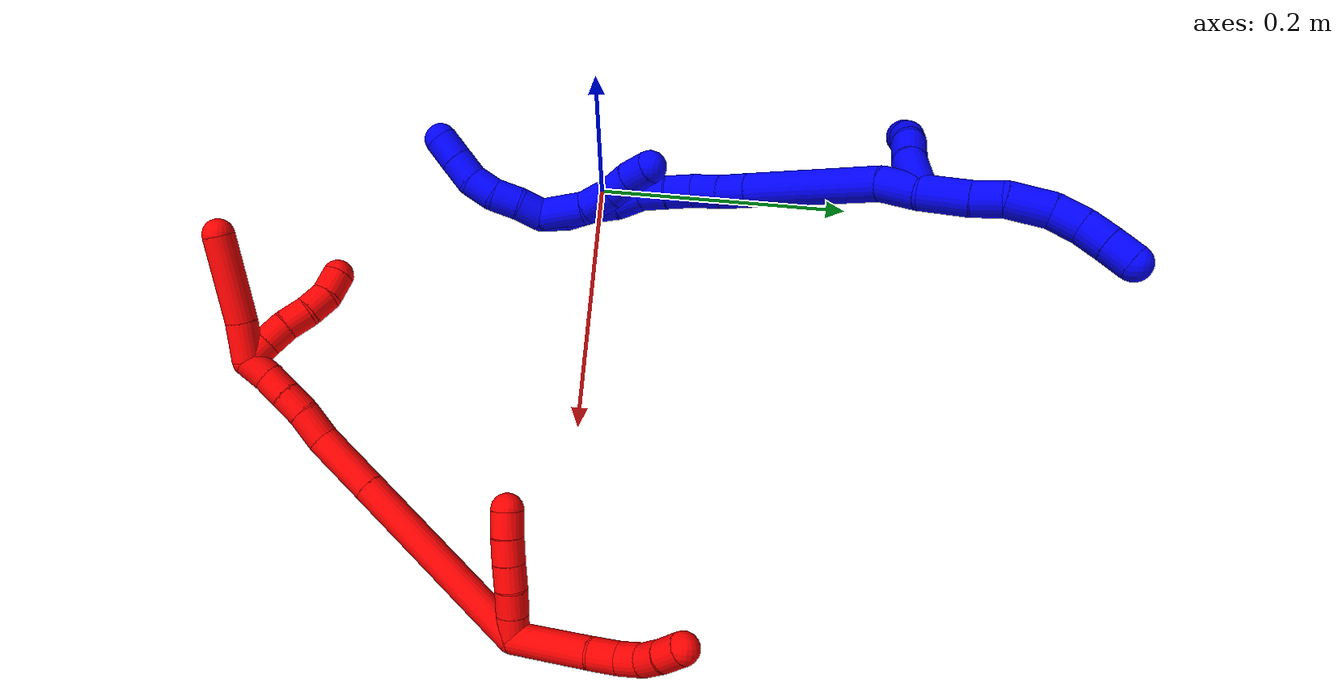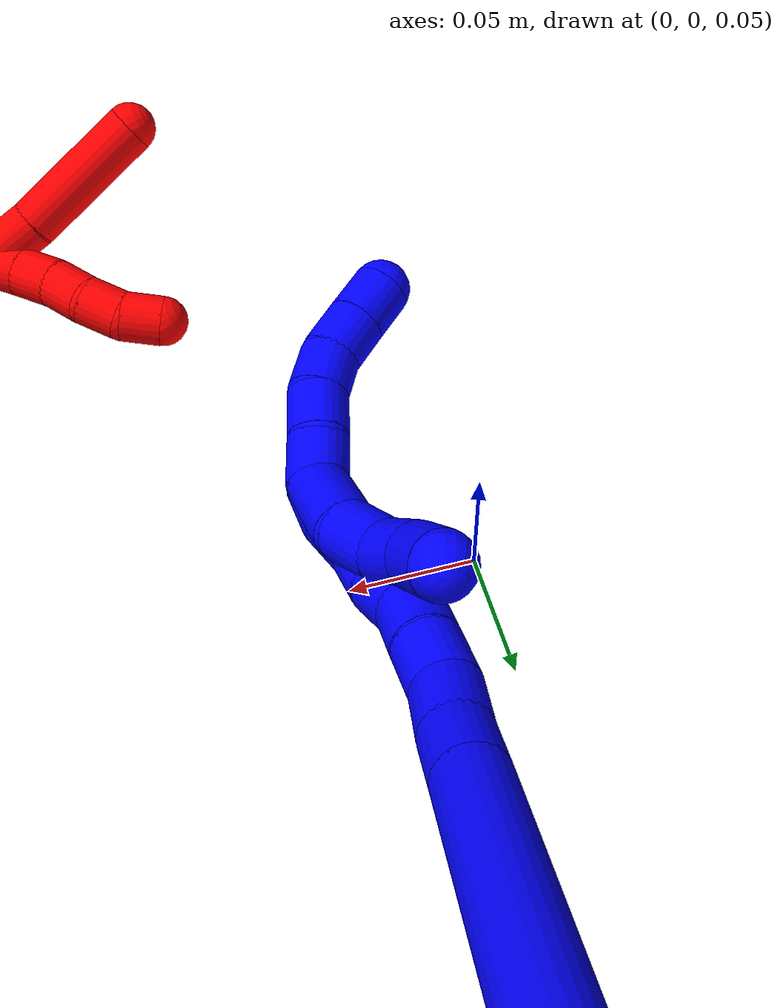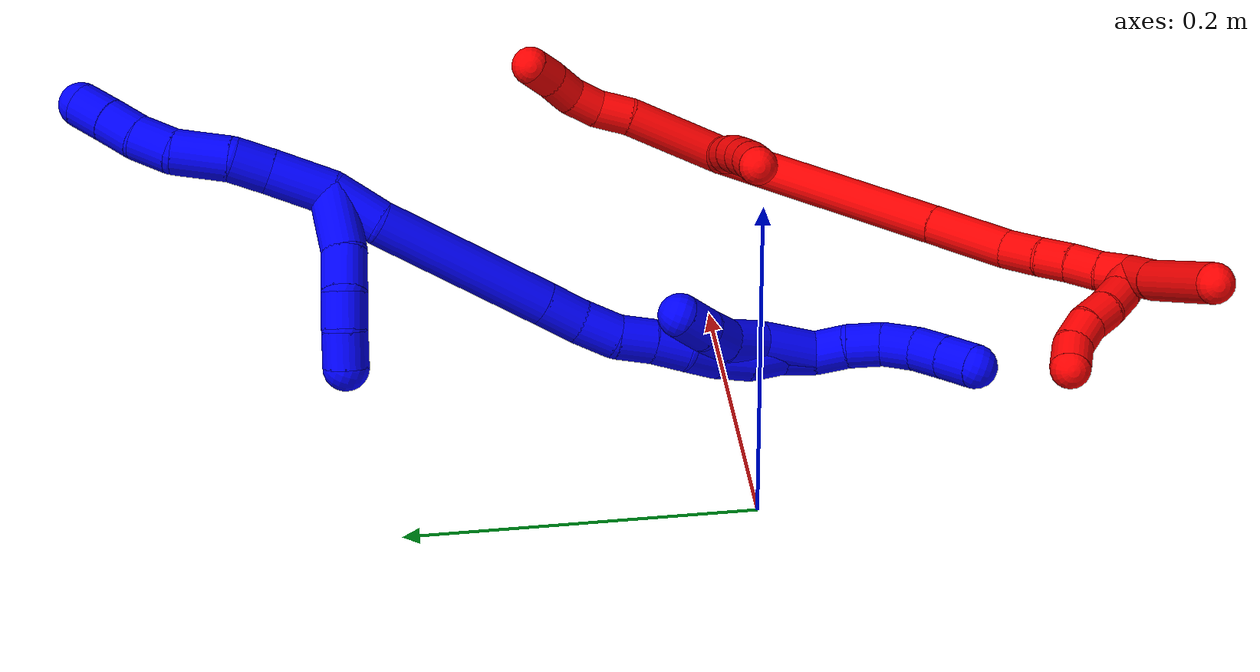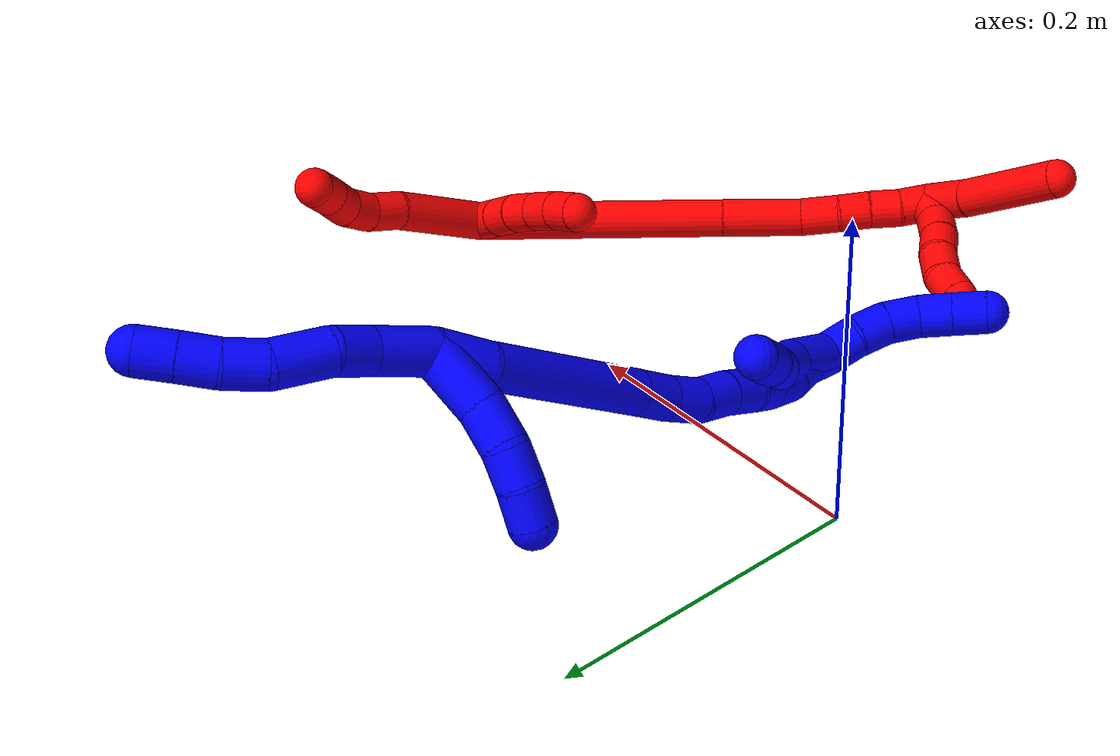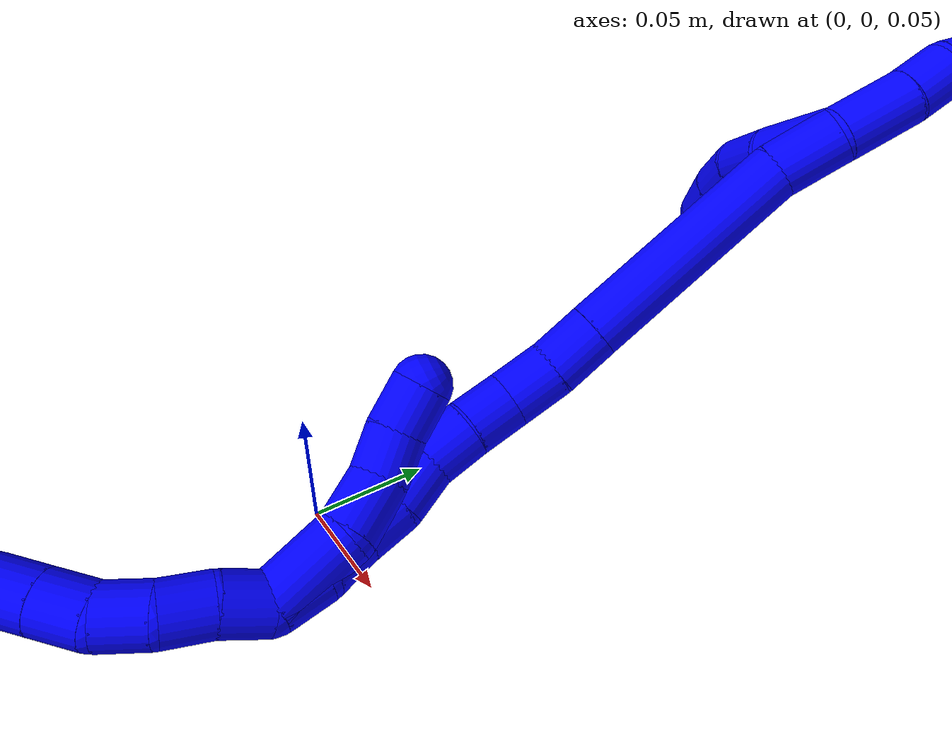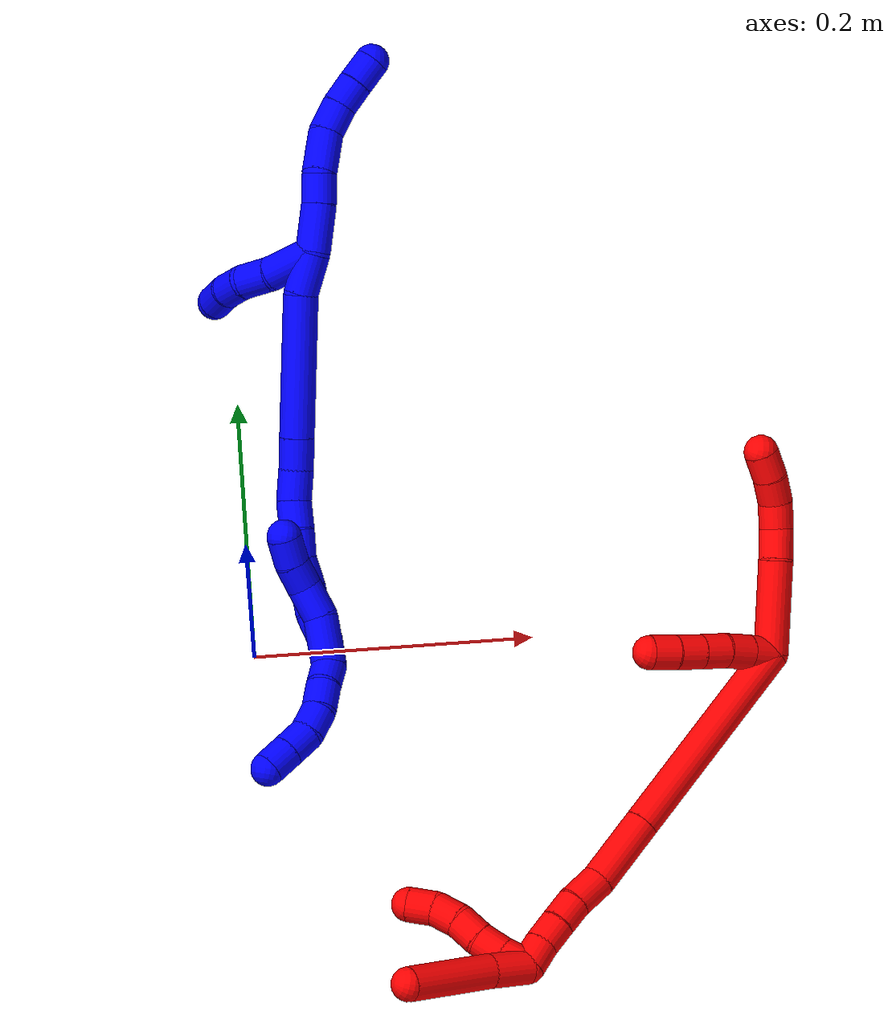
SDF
<sdf version="1.7">
 <world name="default">
  <plugin name="TubeGeneratorPlugin" filename="libtube_generator_plugin.so"/>
  <model name="photoneo_s_sensor">
   <static>1</static>
   <pose>0 0 2 1.57079 1.57079 3.14159</pose>
   <link name="link">
    <inertial><mass>0.1</mass></inertial>
    <sensor name="sensor" type="depth">
     <update_rate>30</update_rate>
     <camera>
      <horizontal_fov>1.22</horizontal_fov>
      <image><width>1920</width><height>1200</height><format>B8G8R8</format></image>
      <clip><near>0.1</near><far>4</far></clip>
      <depth_camera><output>points</output></depth_camera>
     </camera>
     <plugin name="camera_plugin" filename="libgazebo_ros_depth_camera.so">
      <baseline>0.2</baseline>
      <alwaysOn>1</alwaysOn>
      <updateRate>0.0</updateRate>
      <cameraName>camera_ir</cameraName>
      <imageTopicName>/camera/color/image_raw</imageTopicName>
      <cameraInfoTopicName>/camera/color/camera_info</cameraInfoTopicName>
      <depthImageTopicName>/camera/depth/image_raw</depthImageTopicName>
      <depthImageCameraInfoTopicName>/camera/depth/camera_info</depthImageCameraInfoTopicName>
      <pointCloudTopicName>/camera/depth/points</pointCloudTopicName>
      <frameName>fr_optical</frameName>
      <pointCloudCutoff>0.1</pointCloudCutoff>
      <pointCloudCutoffMax>2.0</pointCloudCutoffMax>
      <distortionK1>0</distortionK1>
      <distortionK2>0</distortionK2>
      <distortionK3>0</distortionK3>
      <distortionT1>0</distortionT1>
      <distortionT2>0</distortionT2>
      <CxPrime>0</CxPrime>
      <Cx>0</Cx>
      <Cy>0</Cy>
      <focalLength>0</focalLength>
      <hackBaseline>0</hackBaseline>
     </plugin>
    </sensor>
   </link>
  </model>
  <gravity>0 0 -9.8</gravity>
  <magnetic_field>6e-06 2.3e-05 -4.2e-05</magnetic_field>
  <atmosphere type="adiabatic"/>
  <physics name="default_physics" default="0" type="ode">
   <max_step_size>0.003</max_step_size>
   <real_time_factor>1</real_time_factor>
   <real_time_update_rate>1000</real_time_update_rate>
   <max_contacts>10000</max_contacts>
   <ode>
    <solver>
     <type>quick</type>
     <iters>100</iters>
     <sor>1.3</sor>
     <use_dynamic_moi_rescaling>0</use_dynamic_moi_rescaling>
    </solver>
    <constraints>
     <contact_max_correcting_vel>0</contact_max_correcting_vel>
     <contact_surface_layer>0.001</contact_surface_layer>
     <cfm>0</cfm>
     <erp>0.2</erp>
    </constraints>
   </ode>
  </physics>
  <scene><ambient>0.4 0.4 0.4 1</ambient><background>0.7 0.7 0.7 1</background><shadows>0</shadows></scene>
  <audio><device>default</device></audio>
  <spherical_coordinates>
   <surface_model>EARTH_WGS84</surface_model>
   <latitude_deg>0</latitude_deg>
   <longitude_deg>0</longitude_deg>
   <elevation>0</elevation>
   <heading_deg>0</heading_deg>
  </spherical_coordinates>
  <model name="bin">
   <static>1</static>
   <link name="bottom">
    <collision name="collision-bottom">
     <pose>0 0 -0.01 0 -0 0</pose>
     <geometry><box><size>0.8 0.6 0.02</size></box></geometry>
     <surface>
      <friction><ode><mu>100</mu><mu2>100</mu2></ode></friction>
      <contact><collide_bitmask>65535</collide_bitmask></contact>
     </surface>
    </collision>
   </link>
   <link name="west_wall">
    <collision name="collision-west_wall">
     <pose>-0.41 0 0.1 0 -0 0</pose>
     <geometry><box><size>0.02 0.6 0.2</size></box></geometry>
     <surface>
      <friction><ode><mu>100</mu><mu2>100</mu2></ode></friction>
      <contact><collide_bitmask>65535</collide_bitmask></contact>
     </surface>
    </collision>
   </link>
   <link name="east_wall">
    <collision name="collision-east_wall">
     <pose>0.41 0 0.1 0 -0 0</pose>
     <geometry><box><size>0.02 0.6 0.2</size></box></geometry>
     <surface>
      <friction><ode><mu>100</mu><mu2>100</mu2></ode></friction>
      <contact><collide_bitmask>65535</collide_bitmask></contact>
     </surface>
    </collision>
   </link>
   <link name="south_wall">
    <collision name="collision-south_wall">
     <pose>0 -0.31 0.1 0 -0 0</pose>
     <geometry><box><size>0.8 0.02 0.2</size></box></geometry>
     <surface>
      <friction><ode><mu>100</mu><mu2>100</mu2></ode></friction>
      <contact><collide_bitmask>65535</collide_bitmask></contact>
     </surface>
    </collision>
   </link>
   <link name="north_wall">
    <collision name="collision-north_wall">
     <pose>0 0.31 0.1 0 -0 0</pose>
     <geometry><box><size>0.8 0.02 0.2</size></box></geometry>
     <surface>
      <friction><ode><mu>100</mu><mu2>100</mu2></ode></friction>
      <contact><collide_bitmask>65535</collide_bitmask></contact>
     </surface>
    </collision>
   </link>
  </model>
  <model name="1">
   <static>0</static>
   <link name="1">
    <collision name="collision-cylinder-e_1_2_8">
     <pose>-0.000421 0.000546 0.01757 -0.031074 -0.023938 0.000372</pose>
     <geometry><cylinder><radius>0.0125</radius><length>0.035167</length></cylinder></geometry>
     <surface>
      <friction><ode><mu>1.16</mu><mu2>1.16</mu2><slip1>0</slip1><slip2>0</slip2></ode></friction>
      <contact><ode><kp>1e+06</kp><kd>1</kd><max_vel>0</max_vel><min_depth>0.001</min_depth></ode></contact>
     </surface>
    </collision>
    <visual name="visual-cylinder-e_1_2_8">
     <pose>-0.000421 0.000546 0.01757 -0.031074 -0.023938 0.000372</pose>
     <geometry><cylinder><radius>0.0125</radius><length>0.035167</length></cylinder></geometry>
     <material><ambient>0 0 1 1</ambient></material>
    </visual>
    <collision name="collision-cylinder-e_2_8_9">
     <pose>-0.002362 0.001644 0.045772 -0.051809 -0.141825 0.003681</pose>
     <geometry><cylinder><radius>0.0125</radius><length>0.021507</length></cylinder></geometry>
     <surface>
      <friction><ode><mu>1.16</mu><mu2>1.16</mu2><slip1>0</slip1><slip2>0</slip2></ode></friction>
      <contact><ode><kp>1e+06</kp><kd>1</kd><max_vel>0</max_vel><min_depth>0.001</min_depth></ode></contact>
     </surface>
    </collision>
    <visual name="visual-cylinder-e_2_8_9">
     <pose>-0.002362 0.001644 0.045772 -0.051809 -0.141825 0.003681</pose>
     <geometry><cylinder><radius>0.0125</radius><length>0.021507</length></cylinder></geometry>
     <material><ambient>0 0 1 1</ambient></material>
    </visual>
    <collision name="collision-cylinder-e_3_9_10">
     <pose>-0.002029 0.00593 0.071461 -0.243133 0.118852 -0.014537</pose>
     <geometry><cylinder><radius>0.0125</radius><length>0.03125</length></cylinder></geometry>
     <surface>
      <friction><ode><mu>1.16</mu><mu2>1.16</mu2><slip1>0</slip1><slip2>0</slip2></ode></friction>
      <contact><ode><kp>1e+06</kp><kd>1</kd><max_vel>0</max_vel><min_depth>0.001</min_depth></ode></contact>
     </surface>
    </collision>
    <visual name="visual-cylinder-e_3_9_10">
     <pose>-0.002029 0.00593 0.071461 -0.243133 0.118852 -0.014537</pose>
     <geometry><cylinder><radius>0.0125</radius><length>0.03125</length></cylinder></geometry>
     <material><ambient>0 0 1 1</ambient></material>
    </visual>
    <collision name="collision-cylinder-e_4_10_11">
     <pose>0.003341 0.009643 0.096945 0.00216 0.325387 0.000355</pose>
     <geometry><cylinder><radius>0.0125</radius><length>0.022005</length></cylinder></geometry>
     <surface>
      <friction><ode><mu>1.16</mu><mu2>1.16</mu2><slip1>0</slip1><slip2>0</slip2></ode></friction>
      <contact><ode><kp>1e+06</kp><kd>1</kd><max_vel>0</max_vel><min_depth>0.001</min_depth></ode></contact>
     </surface>
    </collision>
    <visual name="visual-cylinder-e_4_10_11">
     <pose>0.003341 0.009643 0.096945 0.00216 0.325387 0.000355</pose>
     <geometry><cylinder><radius>0.0125</radius><length>0.022005</length></cylinder></geometry>
     <material><ambient>0 0 1 1</ambient></material>
    </visual>
    <collision name="collision-cylinder-e_5_11_12">
     <pose>0.011042 0.008256 0.116379 0.150307 0.430499 0.032922</pose>
     <geometry><cylinder><radius>0.0125</radius><length>0.020053</length></cylinder></geometry>
     <surface>
      <friction><ode><mu>1.16</mu><mu2>1.16</mu2><slip1>0</slip1><slip2>0</slip2></ode></friction>
      <contact><ode><kp>1e+06</kp><kd>1</kd><max_vel>0</max_vel><min_depth>0.001</min_depth></ode></contact>
     </surface>
    </collision>
    <visual name="visual-cylinder-e_5_11_12">
     <pose>0.011042 0.008256 0.116379 0.150307 0.430499 0.032922</pose>
     <geometry><cylinder><radius>0.0125</radius><length>0.020053</length></cylinder></geometry>
     <material><ambient>0 0 1 1</ambient></material>
    </visual>
    <collision name="collision-cylinder-e_6_12_6">
     <pose>0.019726 0.005742 0.134254 0.128875 0.466284 0.030643</pose>
     <geometry><cylinder><radius>0.0125</radius><length>0.020018</length></cylinder></geometry>
     <surface>
      <friction><ode><mu>1.16</mu><mu2>1.16</mu2><slip1>0</slip1><slip2>0</slip2></ode></friction>
      <contact><ode><kp>1e+06</kp><kd>1</kd><max_vel>0</max_vel><min_depth>0.001</min_depth></ode></contact>
     </surface>
    </collision>
    <visual name="visual-cylinder-e_6_12_6">
     <pose>0.019726 0.005742 0.134254 0.128875 0.466284 0.030643</pose>
     <geometry><cylinder><radius>0.0125</radius><length>0.020018</length></cylinder></geometry>
     <material><ambient>0 0 1 1</ambient></material>
    </visual>
    <collision name="collision-cylinder-e_1_2_13">
     <pose>-0.008464 0.013336 -0.008951 -2.16191 -0.484982 0.868748</pose>
     <geometry><cylinder><radius>0.0125</radius><length>0.036311</length></cylinder></geometry>
     <surface>
      <friction><ode><mu>1.16</mu><mu2>1.16</mu2><slip1>0</slip1><slip2>0</slip2></ode></friction>
      <contact><ode><kp>1e+06</kp><kd>1</kd><max_vel>0</max_vel><min_depth>0.001</min_depth></ode></contact>
     </surface>
    </collision>
    <visual name="visual-cylinder-e_1_2_13">
     <pose>-0.008464 0.013336 -0.008951 -2.16191 -0.484982 0.868748</pose>
     <geometry><cylinder><radius>0.0125</radius><length>0.036311</length></cylinder></geometry>
     <material><ambient>0 0 1 1</ambient></material>
    </visual>
    <collision name="collision-cylinder-e_2_13_14">
     <pose>-0.022117 0.036457 -0.021738 -1.9444 -0.458625 0.659445</pose>
     <geometry><cylinder><radius>0.0125</radius><length>0.023441</length></cylinder></geometry>
     <surface>
      <friction><ode><mu>1.16</mu><mu2>1.16</mu2><slip1>0</slip1><slip2>0</slip2></ode></friction>
      <contact><ode><kp>1e+06</kp><kd>1</kd><max_vel>0</max_vel><min_depth>0.001</min_depth></ode></contact>
     </surface>
    </collision>
    <visual name="visual-cylinder-e_2_13_14">
     <pose>-0.022117 0.036457 -0.021738 -1.9444 -0.458625 0.659445</pose>
     <geometry><cylinder><radius>0.0125</radius><length>0.023441</length></cylinder></geometry>
     <material><ambient>0 0 1 1</ambient></material>
    </visual>
    <collision name="collision-cylinder-e_3_14_15">
     <pose>-0.028635 0.055519 -0.02921 -1.94442 -0.132616 0.194106</pose>
     <geometry><cylinder><radius>0.0125</radius><length>0.020106</length></cylinder></geometry>
     <surface>
      <friction><ode><mu>1.16</mu><mu2>1.16</mu2><slip1>0</slip1><slip2>0</slip2></ode></friction>
      <contact><ode><kp>1e+06</kp><kd>1</kd><max_vel>0</max_vel><min_depth>0.001</min_depth></ode></contact>
     </surface>
    </collision>
    <visual name="visual-cylinder-e_3_14_15">
     <pose>-0.028635 0.055519 -0.02921 -1.94442 -0.132616 0.194106</pose>
     <geometry><cylinder><radius>0.0125</radius><length>0.020106</length></cylinder></geometry>
     <material><ambient>0 0 1 1</ambient></material>
    </visual>
    <collision name="collision-cylinder-e_4_15_5">
     <pose>-0.029374 0.074047 -0.036786 -1.9733 0.058646 -0.088676</pose>
     <geometry><cylinder><radius>0.0125</radius><length>0.020142</length></cylinder></geometry>
     <surface>
      <friction><ode><mu>1.16</mu><mu2>1.16</mu2><slip1>0</slip1><slip2>0</slip2></ode></friction>
      <contact><ode><kp>1e+06</kp><kd>1</kd><max_vel>0</max_vel><min_depth>0.001</min_depth></ode></contact>
     </surface>
    </collision>
    <visual name="visual-cylinder-e_4_15_5">
     <pose>-0.029374 0.074047 -0.036786 -1.9733 0.058646 -0.088676</pose>
     <geometry><cylinder><radius>0.0125</radius><length>0.020142</length></cylinder></geometry>
     <material><ambient>0 0 1 1</ambient></material>
    </visual>
    <collision name="collision-cylinder-e_1_2_16">
     <pose>-0.000641 0.002852 -0.01472 -2.95023 -0.042757 0.438419</pose>
     <geometry><cylinder><radius>0.0125</radius><length>0.030014</length></cylinder></geometry>
     <surface>
      <friction><ode><mu>1.16</mu><mu2>1.16</mu2><slip1>0</slip1><slip2>0</slip2></ode></friction>
      <contact><ode><kp>1e+06</kp><kd>1</kd><max_vel>0</max_vel><min_depth>0.001</min_depth></ode></contact>
     </surface>
    </collision>
    <visual name="visual-cylinder-e_1_2_16">
     <pose>-0.000641 0.002852 -0.01472 -2.95023 -0.042757 0.438419</pose>
     <geometry><cylinder><radius>0.0125</radius><length>0.030014</length></cylinder></geometry>
     <material><ambient>0 0 1 1</ambient></material>
    </visual>
    <collision name="collision-cylinder-e_2_16_17">
     <pose>0.00875 0.010555 -0.07921 -3.04441 0.197996 -2.23103</pose>
     <geometry><cylinder><radius>0.0125</radius><length>0.102006</length></cylinder></geometry>
     <surface>
      <friction><ode><mu>1.16</mu><mu2>1.16</mu2><slip1>0</slip1><slip2>0</slip2></ode></friction>
      <contact><ode><kp>1e+06</kp><kd>1</kd><max_vel>0</max_vel><min_depth>0.001</min_depth></ode></contact>
     </surface>
    </collision>
    <visual name="visual-cylinder-e_2_16_17">
     <pose>0.00875 0.010555 -0.07921 -3.04441 0.197996 -2.23103</pose>
     <geometry><cylinder><radius>0.0125</radius><length>0.102006</length></cylinder></geometry>
     <material><ambient>0 0 1 1</ambient></material>
    </visual>
    <collision name="collision-cylinder-e_3_17_18">
     <pose>0.021158 0.016606 -0.140249 -3.03556 0.206678 -2.19567</pose>
     <geometry><cylinder><radius>0.0125</radius><length>0.023157</length></cylinder></geometry>
     <surface>
      <friction><ode><mu>1.16</mu><mu2>1.16</mu2><slip1>0</slip1><slip2>0</slip2></ode></friction>
      <contact><ode><kp>1e+06</kp><kd>1</kd><max_vel>0</max_vel><min_depth>0.001</min_depth></ode></contact>
     </surface>
    </collision>
    <visual name="visual-cylinder-e_3_17_18">
     <pose>0.021158 0.016606 -0.140249 -3.03556 0.206678 -2.19567</pose>
     <geometry><cylinder><radius>0.0125</radius><length>0.023157</length></cylinder></geometry>
     <material><ambient>0 0 1 1</ambient></material>
    </visual>
    <collision name="collision-cylinder-e_4_18_19">
     <pose>0.02485 0.018191 -0.162759 -3.10733 0.116419 -2.56965</pose>
     <geometry><cylinder><radius>0.0125</radius><length>0.022651</length></cylinder></geometry>
     <surface>
      <friction><ode><mu>1.16</mu><mu2>1.16</mu2><slip1>0</slip1><slip2>0</slip2></ode></friction>
      <contact><ode><kp>1e+06</kp><kd>1</kd><max_vel>0</max_vel><min_depth>0.001</min_depth></ode></contact>
     </surface>
    </collision>
    <visual name="visual-cylinder-e_4_18_19">
     <pose>0.02485 0.018191 -0.162759 -3.10733 0.116419 -2.56965</pose>
     <geometry><cylinder><radius>0.0125</radius><length>0.022651</length></cylinder></geometry>
     <material><ambient>0 0 1 1</ambient></material>
    </visual>
    <collision name="collision-cylinder-e_5_19_20">
     <pose>0.028041 0.016237 -0.184077 2.91344 0.179394 1.33104</pose>
     <geometry><cylinder><radius>0.0125</radius><length>0.021025</length></cylinder></geometry>
     <surface>
      <friction><ode><mu>1.16</mu><mu2>1.16</mu2><slip1>0</slip1><slip2>0</slip2></ode></friction>
      <contact><ode><kp>1e+06</kp><kd>1</kd><max_vel>0</max_vel><min_depth>0.001</min_depth></ode></contact>
     </surface>
    </collision>
    <visual name="visual-cylinder-e_5_19_20">
     <pose>0.028041 0.016237 -0.184077 2.91344 0.179394 1.33104</pose>
     <geometry><cylinder><radius>0.0125</radius><length>0.021025</length></cylinder></geometry>
     <material><ambient>0 0 1 1</ambient></material>
    </visual>
    <collision name="collision-cylinder-e_6_20_21">
     <pose>0.031938 0.012711 -0.204078 3.02259 0.199553 2.06804</pose>
     <geometry><cylinder><radius>0.0125</radius><length>0.020397</length></cylinder></geometry>
     <surface>
      <friction><ode><mu>1.16</mu><mu2>1.16</mu2><slip1>0</slip1><slip2>0</slip2></ode></friction>
      <contact><ode><kp>1e+06</kp><kd>1</kd><max_vel>0</max_vel><min_depth>0.001</min_depth></ode></contact>
     </surface>
    </collision>
    <visual name="visual-cylinder-e_6_20_21">
     <pose>0.031938 0.012711 -0.204078 3.02259 0.199553 2.06804</pose>
     <geometry><cylinder><radius>0.0125</radius><length>0.020397</length></cylinder></geometry>
     <material><ambient>0 0 1 1</ambient></material>
    </visual>
    <collision name="collision-cylinder-e_7_21_22">
     <pose>0.038729 0.010524 -0.223157 3.03281 0.477872 2.70181</pose>
     <geometry><cylinder><radius>0.0125</radius><length>0.020738</length></cylinder></geometry>
     <surface>
      <friction><ode><mu>1.16</mu><mu2>1.16</mu2><slip1>0</slip1><slip2>0</slip2></ode></friction>
      <contact><ode><kp>1e+06</kp><kd>1</kd><max_vel>0</max_vel><min_depth>0.001</min_depth></ode></contact>
     </surface>
    </collision>
    <visual name="visual-cylinder-e_7_21_22">
     <pose>0.038729 0.010524 -0.223157 3.03281 0.477872 2.70181</pose>
     <geometry><cylinder><radius>0.0125</radius><length>0.020738</length></cylinder></geometry>
     <material><ambient>0 0 1 1</ambient></material>
    </visual>
    <collision name="collision-cylinder-e_8_22_23">
     <pose>0.04604 0.006966 -0.24164 2.87393 0.256962 1.52954</pose>
     <geometry><cylinder><radius>0.0125</radius><length>0.020007</length></cylinder></geometry>
     <surface>
      <friction><ode><mu>1.16</mu><mu2>1.16</mu2><slip1>0</slip1><slip2>0</slip2></ode></friction>
      <contact><ode><kp>1e+06</kp><kd>1</kd><max_vel>0</max_vel><min_depth>0.001</min_depth></ode></contact>
     </surface>
    </collision>
    <visual name="visual-cylinder-e_8_22_23">
     <pose>0.04604 0.006966 -0.24164 2.87393 0.256962 1.52954</pose>
     <geometry><cylinder><radius>0.0125</radius><length>0.020007</length></cylinder></geometry>
     <material><ambient>0 0 1 1</ambient></material>
    </visual>
    <collision name="collision-cylinder-e_9_23_24">
     <pose>0.052295 -0.000227 -0.259017 2.61911 0.380426 1.24827</pose>
     <geometry><cylinder><radius>0.0125</radius><length>0.020001</length></cylinder></geometry>
     <surface>
      <friction><ode><mu>1.16</mu><mu2>1.16</mu2><slip1>0</slip1><slip2>0</slip2></ode></friction>
      <contact><ode><kp>1e+06</kp><kd>1</kd><max_vel>0</max_vel><min_depth>0.001</min_depth></ode></contact>
     </surface>
    </collision>
    <visual name="visual-cylinder-e_9_23_24">
     <pose>0.052295 -0.000227 -0.259017 2.61911 0.380426 1.24827</pose>
     <geometry><cylinder><radius>0.0125</radius><length>0.020001</length></cylinder></geometry>
     <material><ambient>0 0 1 1</ambient></material>
    </visual>
    <collision name="collision-cylinder-e_10_24_1">
     <pose>0.057642 -0.008237 -0.276336 2.79243 0.16405 0.872325</pose>
     <geometry><cylinder><radius>0.0125</radius><length>0.020005</length></cylinder></geometry>
     <surface>
      <friction><ode><mu>1.16</mu><mu2>1.16</mu2><slip1>0</slip1><slip2>0</slip2></ode></friction>
      <contact><ode><kp>1e+06</kp><kd>1</kd><max_vel>0</max_vel><min_depth>0.001</min_depth></ode></contact>
     </surface>
    </collision>
    <visual name="visual-cylinder-e_10_24_1">
     <pose>0.057642 -0.008237 -0.276336 2.79243 0.16405 0.872325</pose>
     <geometry><cylinder><radius>0.0125</radius><length>0.020005</length></cylinder></geometry>
     <material><ambient>0 0 1 1</ambient></material>
    </visual>
    <collision name="collision-cylinder-e_1_1_25">
     <pose>0.055564 -0.016911 -0.293235 2.53439 -0.380284 -1.1018</pose>
     <geometry><cylinder><radius>0.0125</radius><length>0.02</length></cylinder></geometry>
     <surface>
      <friction><ode><mu>1.16</mu><mu2>1.16</mu2><slip1>0</slip1><slip2>0</slip2></ode></friction>
      <contact><ode><kp>1e+06</kp><kd>1</kd><max_vel>0</max_vel><min_depth>0.001</min_depth></ode></contact>
     </surface>
    </collision>
    <visual name="visual-cylinder-e_1_1_25">
     <pose>0.055564 -0.016911 -0.293235 2.53439 -0.380284 -1.1018</pose>
     <geometry><cylinder><radius>0.0125</radius><length>0.02</length></cylinder></geometry>
     <material><ambient>0 0 1 1</ambient></material>
    </visual>
    <collision name="collision-cylinder-e_2_25_26">
     <pose>0.049397 -0.026383 -0.30961 2.69646 -0.248014 -1.00686</pose>
     <geometry><cylinder><radius>0.0125</radius><length>0.02</length></cylinder></geometry>
     <surface>
      <friction><ode><mu>1.16</mu><mu2>1.16</mu2><slip1>0</slip1><slip2>0</slip2></ode></friction>
      <contact><ode><kp>1e+06</kp><kd>1</kd><max_vel>0</max_vel><min_depth>0.001</min_depth></ode></contact>
     </surface>
    </collision>
    <visual name="visual-cylinder-e_2_25_26">
     <pose>0.049397 -0.026383 -0.30961 2.69646 -0.248014 -1.00686</pose>
     <geometry><cylinder><radius>0.0125</radius><length>0.02</length></cylinder></geometry>
     <material><ambient>0 0 1 1</ambient></material>
    </visual>
    <collision name="collision-cylinder-e_3_26_27">
     <pose>0.042642 -0.032754 -0.327116 2.89571 -0.444512 -2.14086</pose>
     <geometry><cylinder><radius>0.0125</radius><length>0.02</length></cylinder></geometry>
     <surface>
      <friction><ode><mu>1.16</mu><mu2>1.16</mu2><slip1>0</slip1><slip2>0</slip2></ode></friction>
      <contact><ode><kp>1e+06</kp><kd>1</kd><max_vel>0</max_vel><min_depth>0.001</min_depth></ode></contact>
     </surface>
    </collision>
    <visual name="visual-cylinder-e_3_26_27">
     <pose>0.042642 -0.032754 -0.327116 2.89571 -0.444512 -2.14086</pose>
     <geometry><cylinder><radius>0.0125</radius><length>0.02</length></cylinder></geometry>
     <material><ambient>0 0 1 1</ambient></material>
    </visual>
    <collision name="collision-cylinder-e_4_27_28">
     <pose>0.031523 -0.035695 -0.343149 3.03985 -0.750432 -2.88448</pose>
     <geometry><cylinder><radius>0.0125</radius><length>0.02</length></cylinder></geometry>
     <surface>
      <friction><ode><mu>1.16</mu><mu2>1.16</mu2><slip1>0</slip1><slip2>0</slip2></ode></friction>
      <contact><ode><kp>1e+06</kp><kd>1</kd><max_vel>0</max_vel><min_depth>0.001</min_depth></ode></contact>
     </surface>
    </collision>
    <visual name="visual-cylinder-e_4_27_28">
     <pose>0.031523 -0.035695 -0.343149 3.03985 -0.750432 -2.88448</pose>
     <geometry><cylinder><radius>0.0125</radius><length>0.02</length></cylinder></geometry>
     <material><ambient>0 0 1 1</ambient></material>
    </visual>
    <collision name="collision-cylinder-e_5_28_4">
     <pose>0.017855 -0.037037 -0.357687 3.0593 -0.754351 -2.93448</pose>
     <geometry><cylinder><radius>0.0125</radius><length>0.02</length></cylinder></geometry>
     <surface>
      <friction><ode><mu>1.16</mu><mu2>1.16</mu2><slip1>0</slip1><slip2>0</slip2></ode></friction>
      <contact><ode><kp>1e+06</kp><kd>1</kd><max_vel>0</max_vel><min_depth>0.001</min_depth></ode></contact>
     </surface>
    </collision>
    <visual name="visual-cylinder-e_5_28_4">
     <pose>0.017855 -0.037037 -0.357687 3.0593 -0.754351 -2.93448</pose>
     <geometry><cylinder><radius>0.0125</radius><length>0.02</length></cylinder></geometry>
     <material><ambient>0 0 1 1</ambient></material>
    </visual>
    <collision name="collision-cylinder-e_1_1_29">
     <pose>0.054083 -0.008902 -0.268859 -0.16042 -0.296986 0.024048</pose>
     <geometry><cylinder><radius>0.0125</radius><length>0.03549</length></cylinder></geometry>
     <surface>
      <friction><ode><mu>1.16</mu><mu2>1.16</mu2><slip1>0</slip1><slip2>0</slip2></ode></friction>
      <contact><ode><kp>1e+06</kp><kd>1</kd><max_vel>0</max_vel><min_depth>0.001</min_depth></ode></contact>
     </surface>
    </collision>
    <visual name="visual-cylinder-e_1_1_29">
     <pose>0.054083 -0.008902 -0.268859 -0.16042 -0.296986 0.024048</pose>
     <geometry><cylinder><radius>0.0125</radius><length>0.03549</length></cylinder></geometry>
     <material><ambient>0 0 1 1</ambient></material>
    </visual>
    <collision name="collision-cylinder-e_2_29_30">
     <pose>0.041966 -0.003528 -0.242531 -0.271224 -0.608377 0.085619</pose>
     <geometry><cylinder><radius>0.0125</radius><length>0.024231</length></cylinder></geometry>
     <surface>
      <friction><ode><mu>1.16</mu><mu2>1.16</mu2><slip1>0</slip1><slip2>0</slip2></ode></friction>
      <contact><ode><kp>1e+06</kp><kd>1</kd><max_vel>0</max_vel><min_depth>0.001</min_depth></ode></contact>
     </surface>
    </collision>
    <visual name="visual-cylinder-e_2_29_30">
     <pose>0.041966 -0.003528 -0.242531 -0.271224 -0.608377 0.085619</pose>
     <geometry><cylinder><radius>0.0125</radius><length>0.024231</length></cylinder></geometry>
     <material><ambient>0 0 1 1</ambient></material>
    </visual>
    <collision name="collision-cylinder-e_3_30_31">
     <pose>0.028277 -0.001673 -0.225626 0.109875 -0.742535 -0.042813</pose>
     <geometry><cylinder><radius>0.0125</radius><length>0.020008</length></cylinder></geometry>
     <surface>
      <friction><ode><mu>1.16</mu><mu2>1.16</mu2><slip1>0</slip1><slip2>0</slip2></ode></friction>
      <contact><ode><kp>1e+06</kp><kd>1</kd><max_vel>0</max_vel><min_depth>0.001</min_depth></ode></contact>
     </surface>
    </collision>
    <visual name="visual-cylinder-e_3_30_31">
     <pose>0.028277 -0.001673 -0.225626 0.109875 -0.742535 -0.042813</pose>
     <geometry><cylinder><radius>0.0125</radius><length>0.020008</length></cylinder></geometry>
     <material><ambient>0 0 1 1</ambient></material>
    </visual>
    <collision name="collision-cylinder-e_4_31_3">
     <pose>0.016174 -0.003901 -0.209802 0.165515 -0.554753 -0.047224</pose>
     <geometry><cylinder><radius>0.0125</radius><length>0.020272</length></cylinder></geometry>
     <surface>
      <friction><ode><mu>1.16</mu><mu2>1.16</mu2><slip1>0</slip1><slip2>0</slip2></ode></friction>
      <contact><ode><kp>1e+06</kp><kd>1</kd><max_vel>0</max_vel><min_depth>0.001</min_depth></ode></contact>
     </surface>
    </collision>
    <visual name="visual-cylinder-e_4_31_3">
     <pose>0.016174 -0.003901 -0.209802 0.165515 -0.554753 -0.047224</pose>
     <geometry><cylinder><radius>0.0125</radius><length>0.020272</length></cylinder></geometry>
     <material><ambient>0 0 1 1</ambient></material>
    </visual>
    <collision name="collision-sphere-3">
     <pose>0.010835 -0.00532 -0.201304 0 -0 0</pose>
     <geometry><sphere><radius>0.0125</radius></sphere></geometry>
     <surface>
      <friction><ode><mu>1.16</mu><mu2>1.16</mu2><slip1>0</slip1><slip2>0</slip2></ode></friction>
      <contact><ode><kp>1e+06</kp><kd>1</kd><max_vel>0</max_vel><min_depth>0.001</min_depth></ode></contact>
     </surface>
    </collision>
    <visual name="visual-sphere-3">
     <pose>0.010835 -0.00532 -0.201304 0 -0 0</pose>
     <geometry><sphere><radius>0.0125</radius></sphere></geometry>
     <material><ambient>0 0 1 1</ambient></material>
    </visual>
    <collision name="collision-sphere-31">
     <pose>0.021513 -0.002481 -0.2183 0 -0 0</pose>
     <geometry><sphere><radius>0.0125</radius></sphere></geometry>
     <surface>
      <friction><ode><mu>1.16</mu><mu2>1.16</mu2><slip1>0</slip1><slip2>0</slip2></ode></friction>
      <contact><ode><kp>1e+06</kp><kd>1</kd><max_vel>0</max_vel><min_depth>0.001</min_depth></ode></contact>
     </surface>
    </collision>
    <visual name="visual-sphere-31">
     <pose>0.021513 -0.002481 -0.2183 0 -0 0</pose>
     <geometry><sphere><radius>0.0125</radius></sphere></geometry>
     <material><ambient>0 0 1 1</ambient></material>
    </visual>
    <collision name="collision-sphere-30">
     <pose>0.035041 -0.000865 -0.232953 0 -0 0</pose>
     <geometry><sphere><radius>0.0125</radius></sphere></geometry>
     <surface>
      <friction><ode><mu>1.16</mu><mu2>1.16</mu2><slip1>0</slip1><slip2>0</slip2></ode></friction>
      <contact><ode><kp>1e+06</kp><kd>1</kd><max_vel>0</max_vel><min_depth>0.001</min_depth></ode></contact>
     </surface>
    </collision>
    <visual name="visual-sphere-30">
     <pose>0.035041 -0.000865 -0.232953 0 -0 0</pose>
     <geometry><sphere><radius>0.0125</radius></sphere></geometry>
     <material><ambient>0 0 1 1</ambient></material>
    </visual>
    <collision name="collision-sphere-29">
     <pose>0.04889 -0.006192 -0.252109 0 -0 0</pose>
     <geometry><sphere><radius>0.0125</radius></sphere></geometry>
     <surface>
      <friction><ode><mu>1.16</mu><mu2>1.16</mu2><slip1>0</slip1><slip2>0</slip2></ode></friction>
      <contact><ode><kp>1e+06</kp><kd>1</kd><max_vel>0</max_vel><min_depth>0.001</min_depth></ode></contact>
     </surface>
    </collision>
    <visual name="visual-sphere-29">
     <pose>0.04889 -0.006192 -0.252109 0 -0 0</pose>
     <geometry><sphere><radius>0.0125</radius></sphere></geometry>
     <material><ambient>0 0 1 1</ambient></material>
    </visual>
    <collision name="collision-sphere-4">
     <pose>0.011007 -0.037636 -0.36495 0 -0 0</pose>
     <geometry><sphere><radius>0.0125</radius></sphere></geometry>
     <surface>
      <friction><ode><mu>1.16</mu><mu2>1.16</mu2><slip1>0</slip1><slip2>0</slip2></ode></friction>
      <contact><ode><kp>1e+06</kp><kd>1</kd><max_vel>0</max_vel><min_depth>0.001</min_depth></ode></contact>
     </surface>
    </collision>
    <visual name="visual-sphere-4">
     <pose>0.011007 -0.037636 -0.36495 0 -0 0</pose>
     <geometry><sphere><radius>0.0125</radius></sphere></geometry>
     <material><ambient>0 0 1 1</ambient></material>
    </visual>
    <collision name="collision-sphere-28">
     <pose>0.024703 -0.036438 -0.350425 0 -0 0</pose>
     <geometry><sphere><radius>0.0125</radius></sphere></geometry>
     <surface>
      <friction><ode><mu>1.16</mu><mu2>1.16</mu2><slip1>0</slip1><slip2>0</slip2></ode></friction>
      <contact><ode><kp>1e+06</kp><kd>1</kd><max_vel>0</max_vel><min_depth>0.001</min_depth></ode></contact>
     </surface>
    </collision>
    <visual name="visual-sphere-28">
     <pose>0.024703 -0.036438 -0.350425 0 -0 0</pose>
     <geometry><sphere><radius>0.0125</radius></sphere></geometry>
     <material><ambient>0 0 1 1</ambient></material>
    </visual>
    <collision name="collision-sphere-27">
     <pose>0.038342 -0.034952 -0.335873 0 -0 0</pose>
     <geometry><sphere><radius>0.0125</radius></sphere></geometry>
     <surface>
      <friction><ode><mu>1.16</mu><mu2>1.16</mu2><slip1>0</slip1><slip2>0</slip2></ode></friction>
      <contact><ode><kp>1e+06</kp><kd>1</kd><max_vel>0</max_vel><min_depth>0.001</min_depth></ode></contact>
     </surface>
    </collision>
    <visual name="visual-sphere-27">
     <pose>0.038342 -0.034952 -0.335873 0 -0 0</pose>
     <geometry><sphere><radius>0.0125</radius></sphere></geometry>
     <material><ambient>0 0 1 1</ambient></material>
    </visual>
    <collision name="collision-sphere-26">
     <pose>0.046942 -0.030557 -0.318359 0 -0 0</pose>
     <geometry><sphere><radius>0.0125</radius></sphere></geometry>
     <surface>
      <friction><ode><mu>1.16</mu><mu2>1.16</mu2><slip1>0</slip1><slip2>0</slip2></ode></friction>
      <contact><ode><kp>1e+06</kp><kd>1</kd><max_vel>0</max_vel><min_depth>0.001</min_depth></ode></contact>
     </surface>
    </collision>
    <visual name="visual-sphere-26">
     <pose>0.046942 -0.030557 -0.318359 0 -0 0</pose>
     <geometry><sphere><radius>0.0125</radius></sphere></geometry>
     <material><ambient>0 0 1 1</ambient></material>
    </visual>
    <collision name="collision-sphere-25">
     <pose>0.051852 -0.022209 -0.300861 0 -0 0</pose>
     <geometry><sphere><radius>0.0125</radius></sphere></geometry>
     <surface>
      <friction><ode><mu>1.16</mu><mu2>1.16</mu2><slip1>0</slip1><slip2>0</slip2></ode></friction>
      <contact><ode><kp>1e+06</kp><kd>1</kd><max_vel>0</max_vel><min_depth>0.001</min_depth></ode></contact>
     </surface>
    </collision>
    <visual name="visual-sphere-25">
     <pose>0.051852 -0.022209 -0.300861 0 -0 0</pose>
     <geometry><sphere><radius>0.0125</radius></sphere></geometry>
     <material><ambient>0 0 1 1</ambient></material>
    </visual>
    <collision name="collision-sphere-1">
     <pose>0.059276 -0.011613 -0.285609 0 -0 0</pose>
     <geometry><sphere><radius>0.0125</radius></sphere></geometry>
     <surface>
      <friction><ode><mu>1.16</mu><mu2>1.16</mu2><slip1>0</slip1><slip2>0</slip2></ode></friction>
      <contact><ode><kp>1e+06</kp><kd>1</kd><max_vel>0</max_vel><min_depth>0.001</min_depth></ode></contact>
     </surface>
    </collision>
    <visual name="visual-sphere-1">
     <pose>0.059276 -0.011613 -0.285609 0 -0 0</pose>
     <geometry><sphere><radius>0.0125</radius></sphere></geometry>
     <material><ambient>0 0 1 1</ambient></material>
    </visual>
    <collision name="collision-sphere-24">
     <pose>0.056009 -0.004861 -0.267064 0 -0 0</pose>
     <geometry><sphere><radius>0.0125</radius></sphere></geometry>
     <surface>
      <friction><ode><mu>1.16</mu><mu2>1.16</mu2><slip1>0</slip1><slip2>0</slip2></ode></friction>
      <contact><ode><kp>1e+06</kp><kd>1</kd><max_vel>0</max_vel><min_depth>0.001</min_depth></ode></contact>
     </surface>
    </collision>
    <visual name="visual-sphere-24">
     <pose>0.056009 -0.004861 -0.267064 0 -0 0</pose>
     <geometry><sphere><radius>0.0125</radius></sphere></geometry>
     <material><ambient>0 0 1 1</ambient></material>
    </visual>
    <collision name="collision-sphere-23">
     <pose>0.048582 0.004407 -0.250971 0 -0 0</pose>
     <geometry><sphere><radius>0.0125</radius></sphere></geometry>
     <surface>
      <friction><ode><mu>1.16</mu><mu2>1.16</mu2><slip1>0</slip1><slip2>0</slip2></ode></friction>
      <contact><ode><kp>1e+06</kp><kd>1</kd><max_vel>0</max_vel><min_depth>0.001</min_depth></ode></contact>
     </surface>
    </collision>
    <visual name="visual-sphere-23">
     <pose>0.048582 0.004407 -0.250971 0 -0 0</pose>
     <geometry><sphere><radius>0.0125</radius></sphere></geometry>
     <material><ambient>0 0 1 1</ambient></material>
    </visual>
    <collision name="collision-sphere-22">
     <pose>0.043497 0.009525 -0.23231 0 -0 0</pose>
     <geometry><sphere><radius>0.0125</radius></sphere></geometry>
     <surface>
      <friction><ode><mu>1.16</mu><mu2>1.16</mu2><slip1>0</slip1><slip2>0</slip2></ode></friction>
      <contact><ode><kp>1e+06</kp><kd>1</kd><max_vel>0</max_vel><min_depth>0.001</min_depth></ode></contact>
     </surface>
    </collision>
    <visual name="visual-sphere-22">
     <pose>0.043497 0.009525 -0.23231 0 -0 0</pose>
     <geometry><sphere><radius>0.0125</radius></sphere></geometry>
     <material><ambient>0 0 1 1</ambient></material>
    </visual>
    <collision name="collision-sphere-21">
     <pose>0.03396 0.011524 -0.214003 0 -0 0</pose>
     <geometry><sphere><radius>0.0125</radius></sphere></geometry>
     <surface>
      <friction><ode><mu>1.16</mu><mu2>1.16</mu2><slip1>0</slip1><slip2>0</slip2></ode></friction>
      <contact><ode><kp>1e+06</kp><kd>1</kd><max_vel>0</max_vel><min_depth>0.001</min_depth></ode></contact>
     </surface>
    </collision>
    <visual name="visual-sphere-21">
     <pose>0.03396 0.011524 -0.214003 0 -0 0</pose>
     <geometry><sphere><radius>0.0125</radius></sphere></geometry>
     <material><ambient>0 0 1 1</ambient></material>
    </visual>
    <collision name="collision-sphere-12">
     <pose>0.015227 0.006891 0.125388 0 -0 0</pose>
     <geometry><sphere><radius>0.0125</radius></sphere></geometry>
     <surface>
      <friction><ode><mu>1.16</mu><mu2>1.16</mu2><slip1>0</slip1><slip2>0</slip2></ode></friction>
      <contact><ode><kp>1e+06</kp><kd>1</kd><max_vel>0</max_vel><min_depth>0.001</min_depth></ode></contact>
     </surface>
    </collision>
    <visual name="visual-sphere-12">
     <pose>0.015227 0.006891 0.125388 0 -0 0</pose>
     <geometry><sphere><radius>0.0125</radius></sphere></geometry>
     <material><ambient>0 0 1 1</ambient></material>
    </visual>
    <collision name="collision-sphere-11">
     <pose>0.006858 0.00962 0.10737 0 -0 0</pose>
     <geometry><sphere><radius>0.0125</radius></sphere></geometry>
     <surface>
      <friction><ode><mu>1.16</mu><mu2>1.16</mu2><slip1>0</slip1><slip2>0</slip2></ode></friction>
      <contact><ode><kp>1e+06</kp><kd>1</kd><max_vel>0</max_vel><min_depth>0.001</min_depth></ode></contact>
     </surface>
    </collision>
    <visual name="visual-sphere-11">
     <pose>0.006858 0.00962 0.10737 0 -0 0</pose>
     <geometry><sphere><radius>0.0125</radius></sphere></geometry>
     <material><ambient>0 0 1 1</ambient></material>
    </visual>
    <collision name="collision-sphere-10">
     <pose>-0.000176 0.009665 0.08652 0 -0 0</pose>
     <geometry><sphere><radius>0.0125</radius></sphere></geometry>
     <surface>
      <friction><ode><mu>1.16</mu><mu2>1.16</mu2><slip1>0</slip1><slip2>0</slip2></ode></friction>
      <contact><ode><kp>1e+06</kp><kd>1</kd><max_vel>0</max_vel><min_depth>0.001</min_depth></ode></contact>
     </surface>
    </collision>
    <visual name="visual-sphere-10">
     <pose>-0.000176 0.009665 0.08652 0 -0 0</pose>
     <geometry><sphere><radius>0.0125</radius></sphere></geometry>
     <material><ambient>0 0 1 1</ambient></material>
    </visual>
    <collision name="collision-sphere-9">
     <pose>-0.003882 0.002195 0.056403 0 -0 0</pose>
     <geometry><sphere><radius>0.0125</radius></sphere></geometry>
     <surface>
      <friction><ode><mu>1.16</mu><mu2>1.16</mu2><slip1>0</slip1><slip2>0</slip2></ode></friction>
      <contact><ode><kp>1e+06</kp><kd>1</kd><max_vel>0</max_vel><min_depth>0.001</min_depth></ode></contact>
     </surface>
    </collision>
    <visual name="visual-sphere-9">
     <pose>-0.003882 0.002195 0.056403 0 -0 0</pose>
     <geometry><sphere><radius>0.0125</radius></sphere></geometry>
     <material><ambient>0 0 1 1</ambient></material>
    </visual>
    <collision name="collision-sphere-2">
     <geometry><sphere><radius>0.0125</radius></sphere></geometry>
     <surface>
      <friction><ode><mu>1.16</mu><mu2>1.16</mu2><slip1>0</slip1><slip2>0</slip2></ode></friction>
      <contact><ode><kp>1e+06</kp><kd>1</kd><max_vel>0</max_vel><min_depth>0.001</min_depth></ode></contact>
     </surface>
    </collision>
    <visual name="visual-sphere-2">
     <geometry><sphere><radius>0.0125</radius></sphere></geometry>
     <material><ambient>0 0 1 1</ambient></material>
    </visual>
    <collision name="collision-sphere-19">
     <pose>0.026165 0.018576 -0.174001 0 -0 0</pose>
     <geometry><sphere><radius>0.0125</radius></sphere></geometry>
     <surface>
      <friction><ode><mu>1.16</mu><mu2>1.16</mu2><slip1>0</slip1><slip2>0</slip2></ode></friction>
      <contact><ode><kp>1e+06</kp><kd>1</kd><max_vel>0</max_vel><min_depth>0.001</min_depth></ode></contact>
     </surface>
    </collision>
    <visual name="visual-sphere-19">
     <pose>0.026165 0.018576 -0.174001 0 -0 0</pose>
     <geometry><sphere><radius>0.0125</radius></sphere></geometry>
     <material><ambient>0 0 1 1</ambient></material>
    </visual>
    <collision name="collision-sphere-8">
     <pose>-0.000842 0.001092 0.03514 0 -0 0</pose>
     <geometry><sphere><radius>0.0125</radius></sphere></geometry>
     <surface>
      <friction><ode><mu>1.16</mu><mu2>1.16</mu2><slip1>0</slip1><slip2>0</slip2></ode></friction>
      <contact><ode><kp>1e+06</kp><kd>1</kd><max_vel>0</max_vel><min_depth>0.001</min_depth></ode></contact>
     </surface>
    </collision>
    <visual name="visual-sphere-8">
     <pose>-0.000842 0.001092 0.03514 0 -0 0</pose>
     <geometry><sphere><radius>0.0125</radius></sphere></geometry>
     <material><ambient>0 0 1 1</ambient></material>
    </visual>
    <collision name="collision-sphere-6">
     <pose>0.024226 0.004593 0.14312 0 -0 0</pose>
     <geometry><sphere><radius>0.0125</radius></sphere></geometry>
     <surface>
      <friction><ode><mu>1.16</mu><mu2>1.16</mu2><slip1>0</slip1><slip2>0</slip2></ode></friction>
      <contact><ode><kp>1e+06</kp><kd>1</kd><max_vel>0</max_vel><min_depth>0.001</min_depth></ode></contact>
     </surface>
    </collision>
    <visual name="visual-sphere-6">
     <pose>0.024226 0.004593 0.14312 0 -0 0</pose>
     <geometry><sphere><radius>0.0125</radius></sphere></geometry>
     <material><ambient>0 0 1 1</ambient></material>
    </visual>
    <collision name="collision-sphere-13">
     <pose>-0.016928 0.026673 -0.017902 0 -0 0</pose>
     <geometry><sphere><radius>0.0125</radius></sphere></geometry>
     <surface>
      <friction><ode><mu>1.16</mu><mu2>1.16</mu2><slip1>0</slip1><slip2>0</slip2></ode></friction>
      <contact><ode><kp>1e+06</kp><kd>1</kd><max_vel>0</max_vel><min_depth>0.001</min_depth></ode></contact>
     </surface>
    </collision>
    <visual name="visual-sphere-13">
     <pose>-0.016928 0.026673 -0.017902 0 -0 0</pose>
     <geometry><sphere><radius>0.0125</radius></sphere></geometry>
     <material><ambient>0 0 1 1</ambient></material>
    </visual>
    <collision name="collision-sphere-14">
     <pose>-0.027306 0.046242 -0.025573 0 -0 0</pose>
     <geometry><sphere><radius>0.0125</radius></sphere></geometry>
     <surface>
      <friction><ode><mu>1.16</mu><mu2>1.16</mu2><slip1>0</slip1><slip2>0</slip2></ode></friction>
      <contact><ode><kp>1e+06</kp><kd>1</kd><max_vel>0</max_vel><min_depth>0.001</min_depth></ode></contact>
     </surface>
    </collision>
    <visual name="visual-sphere-14">
     <pose>-0.027306 0.046242 -0.025573 0 -0 0</pose>
     <geometry><sphere><radius>0.0125</radius></sphere></geometry>
     <material><ambient>0 0 1 1</ambient></material>
    </visual>
    <collision name="collision-sphere-15">
     <pose>-0.029964 0.064797 -0.032847 0 -0 0</pose>
     <geometry><sphere><radius>0.0125</radius></sphere></geometry>
     <surface>
      <friction><ode><mu>1.16</mu><mu2>1.16</mu2><slip1>0</slip1><slip2>0</slip2></ode></friction>
      <contact><ode><kp>1e+06</kp><kd>1</kd><max_vel>0</max_vel><min_depth>0.001</min_depth></ode></contact>
     </surface>
    </collision>
    <visual name="visual-sphere-15">
     <pose>-0.029964 0.064797 -0.032847 0 -0 0</pose>
     <geometry><sphere><radius>0.0125</radius></sphere></geometry>
     <material><ambient>0 0 1 1</ambient></material>
    </visual>
    <collision name="collision-sphere-5">
     <pose>-0.028784 0.083297 -0.040724 0 -0 0</pose>
     <geometry><sphere><radius>0.0125</radius></sphere></geometry>
     <surface>
      <friction><ode><mu>1.16</mu><mu2>1.16</mu2><slip1>0</slip1><slip2>0</slip2></ode></friction>
      <contact><ode><kp>1e+06</kp><kd>1</kd><max_vel>0</max_vel><min_depth>0.001</min_depth></ode></contact>
     </surface>
    </collision>
    <visual name="visual-sphere-5">
     <pose>-0.028784 0.083297 -0.040724 0 -0 0</pose>
     <geometry><sphere><radius>0.0125</radius></sphere></geometry>
     <material><ambient>0 0 1 1</ambient></material>
    </visual>
    <collision name="collision-sphere-16">
     <pose>-0.001283 0.005703 -0.029439 0 -0 0</pose>
     <geometry><sphere><radius>0.0125</radius></sphere></geometry>
     <surface>
      <friction><ode><mu>1.16</mu><mu2>1.16</mu2><slip1>0</slip1><slip2>0</slip2></ode></friction>
      <contact><ode><kp>1e+06</kp><kd>1</kd><max_vel>0</max_vel><min_depth>0.001</min_depth></ode></contact>
     </surface>
    </collision>
    <visual name="visual-sphere-16">
     <pose>-0.001283 0.005703 -0.029439 0 -0 0</pose>
     <geometry><sphere><radius>0.0125</radius></sphere></geometry>
     <material><ambient>0 0 1 1</ambient></material>
    </visual>
    <collision name="collision-sphere-17">
     <pose>0.018782 0.015407 -0.128981 0 -0 0</pose>
     <geometry><sphere><radius>0.0125</radius></sphere></geometry>
     <surface>
      <friction><ode><mu>1.16</mu><mu2>1.16</mu2><slip1>0</slip1><slip2>0</slip2></ode></friction>
      <contact><ode><kp>1e+06</kp><kd>1</kd><max_vel>0</max_vel><min_depth>0.001</min_depth></ode></contact>
     </surface>
    </collision>
    <visual name="visual-sphere-17">
     <pose>0.018782 0.015407 -0.128981 0 -0 0</pose>
     <geometry><sphere><radius>0.0125</radius></sphere></geometry>
     <material><ambient>0 0 1 1</ambient></material>
    </visual>
    <collision name="collision-sphere-18">
     <pose>0.023534 0.017806 -0.151517 0 -0 0</pose>
     <geometry><sphere><radius>0.0125</radius></sphere></geometry>
     <surface>
      <friction><ode><mu>1.16</mu><mu2>1.16</mu2><slip1>0</slip1><slip2>0</slip2></ode></friction>
      <contact><ode><kp>1e+06</kp><kd>1</kd><max_vel>0</max_vel><min_depth>0.001</min_depth></ode></contact>
     </surface>
    </collision>
    <visual name="visual-sphere-18">
     <pose>0.023534 0.017806 -0.151517 0 -0 0</pose>
     <geometry><sphere><radius>0.0125</radius></sphere></geometry>
     <material><ambient>0 0 1 1</ambient></material>
    </visual>
    <collision name="collision-sphere-20">
     <pose>0.029917 0.013897 -0.194153 0 -0 0</pose>
     <geometry><sphere><radius>0.0125</radius></sphere></geometry>
     <surface>
      <friction><ode><mu>1.16</mu><mu2>1.16</mu2><slip1>0</slip1><slip2>0</slip2></ode></friction>
      <contact><ode><kp>1e+06</kp><kd>1</kd><max_vel>0</max_vel><min_depth>0.001</min_depth></ode></contact>
     </surface>
    </collision>
    <visual name="visual-sphere-20">
     <pose>0.029917 0.013897 -0.194153 0 -0 0</pose>
     <geometry><sphere><radius>0.0125</radius></sphere></geometry>
     <material><ambient>0 0 1 1</ambient></material>
    </visual>
    <inertial>
     <pose>0.017903 0.00525 -0.122179 0 -0 0</pose>
     <mass>0.75</mass>
     <inertia>
      <ixx>-9.3e-05</ixx>
      <ixy>0</ixy>
      <ixz>0</ixz>
      <iyy>2.5e-05</iyy>
      <iyz>0</iyz>
      <izz>-4.1e-05</izz>
     </inertia>
    </inertial>
   </link>
   <pose>0.061077 0.225752 0.189543 -1.1496 0.528732 -0.02447</pose>
  </model>
  <model name="2">
   <static>0</static>
   <link name="2">
    <collision name="collision-cylinder-e_1_2_8">
     <pose>0.008759 0.032255 -0.004434 -1.70742 0.262809 -0.30087</pose>
     <geometry><cylinder><radius>0.0125</radius><length>0.067432</length></cylinder></geometry>
     <surface>
      <friction><ode><mu>1.16</mu><mu2>1.16</mu2><slip1>0</slip1><slip2>0</slip2></ode></friction>
      <contact><ode><kp>1e+06</kp><kd>1</kd><max_vel>0</max_vel><min_depth>0.001</min_depth></ode></contact>
     </surface>
    </collision>
    <visual name="visual-cylinder-e_1_2_8">
     <pose>0.008759 0.032255 -0.004434 -1.70742 0.262809 -0.30087</pose>
     <geometry><cylinder><radius>0.0125</radius><length>0.067432</length></cylinder></geometry>
     <material><ambient>1 0 0 1</ambient></material>
    </visual>
    <collision name="collision-cylinder-e_2_8_9">
     <pose>0.02217 0.074709 -0.00988 -1.66955 0.426056 -0.468822</pose>
     <geometry><cylinder><radius>0.0125</radius><length>0.022511</length></cylinder></geometry>
     <surface>
      <friction><ode><mu>1.16</mu><mu2>1.16</mu2><slip1>0</slip1><slip2>0</slip2></ode></friction>
      <contact><ode><kp>1e+06</kp><kd>1</kd><max_vel>0</max_vel><min_depth>0.001</min_depth></ode></contact>
     </surface>
    </collision>
    <visual name="visual-cylinder-e_2_8_9">
     <pose>0.02217 0.074709 -0.00988 -1.66955 0.426056 -0.468822</pose>
     <geometry><cylinder><radius>0.0125</radius><length>0.022511</length></cylinder></geometry>
     <material><ambient>1 0 0 1</ambient></material>
    </visual>
    <collision name="collision-cylinder-e_3_9_10">
     <pose>0.028751 0.094375 -0.013497 -1.83958 0.194036 -0.254136</pose>
     <geometry><cylinder><radius>0.0125</radius><length>0.020013</length></cylinder></geometry>
     <surface>
      <friction><ode><mu>1.16</mu><mu2>1.16</mu2><slip1>0</slip1><slip2>0</slip2></ode></friction>
      <contact><ode><kp>1e+06</kp><kd>1</kd><max_vel>0</max_vel><min_depth>0.001</min_depth></ode></contact>
     </surface>
    </collision>
    <visual name="visual-cylinder-e_3_9_10">
     <pose>0.028751 0.094375 -0.013497 -1.83958 0.194036 -0.254136</pose>
     <geometry><cylinder><radius>0.0125</radius><length>0.020013</length></cylinder></geometry>
     <material><ambient>1 0 0 1</ambient></material>
    </visual>
    <collision name="collision-cylinder-e_4_10_11">
     <pose>0.030256 0.112497 -0.021106 -2.09467 -0.042432 0.073496</pose>
     <geometry><cylinder><radius>0.0125</radius><length>0.020012</length></cylinder></geometry>
     <surface>
      <friction><ode><mu>1.16</mu><mu2>1.16</mu2><slip1>0</slip1><slip2>0</slip2></ode></friction>
      <contact><ode><kp>1e+06</kp><kd>1</kd><max_vel>0</max_vel><min_depth>0.001</min_depth></ode></contact>
     </surface>
    </collision>
    <visual name="visual-cylinder-e_4_10_11">
     <pose>0.030256 0.112497 -0.021106 -2.09467 -0.042432 0.073496</pose>
     <geometry><cylinder><radius>0.0125</radius><length>0.020012</length></cylinder></geometry>
     <material><ambient>1 0 0 1</ambient></material>
    </visual>
    <collision name="collision-cylinder-e_5_11_6">
     <pose>0.030221 0.129287 -0.031938 -2.19279 0.038818 -0.075566</pose>
     <geometry><cylinder><radius>0.0125</radius><length>0.020033</length></cylinder></geometry>
     <surface>
      <friction><ode><mu>1.16</mu><mu2>1.16</mu2><slip1>0</slip1><slip2>0</slip2></ode></friction>
      <contact><ode><kp>1e+06</kp><kd>1</kd><max_vel>0</max_vel><min_depth>0.001</min_depth></ode></contact>
     </surface>
    </collision>
    <visual name="visual-cylinder-e_5_11_6">
     <pose>0.030221 0.129287 -0.031938 -2.19279 0.038818 -0.075566</pose>
     <geometry><cylinder><radius>0.0125</radius><length>0.020033</length></cylinder></geometry>
     <material><ambient>1 0 0 1</ambient></material>
    </visual>
    <collision name="collision-cylinder-e_1_2_12">
     <pose>-0.001685 -0.000304 -0.009852 3.11076 -0.16927 -2.78203</pose>
     <geometry><cylinder><radius>0.0125</radius><length>0.02</length></cylinder></geometry>
     <surface>
      <friction><ode><mu>1.16</mu><mu2>1.16</mu2><slip1>0</slip1><slip2>0</slip2></ode></friction>
      <contact><ode><kp>1e+06</kp><kd>1</kd><max_vel>0</max_vel><min_depth>0.001</min_depth></ode></contact>
     </surface>
    </collision>
    <visual name="visual-cylinder-e_1_2_12">
     <pose>-0.001685 -0.000304 -0.009852 3.11076 -0.16927 -2.78203</pose>
     <geometry><cylinder><radius>0.0125</radius><length>0.02</length></cylinder></geometry>
     <material><ambient>1 0 0 1</ambient></material>
    </visual>
    <collision name="collision-cylinder-e_2_12_13">
     <pose>-0.005216 -0.001068 -0.029522 3.09475 -0.185728 -2.64876</pose>
     <geometry><cylinder><radius>0.0125</radius><length>0.02</length></cylinder></geometry>
     <surface>
      <friction><ode><mu>1.16</mu><mu2>1.16</mu2><slip1>0</slip1><slip2>0</slip2></ode></friction>
      <contact><ode><kp>1e+06</kp><kd>1</kd><max_vel>0</max_vel><min_depth>0.001</min_depth></ode></contact>
     </surface>
    </collision>
    <visual name="visual-cylinder-e_2_12_13">
     <pose>-0.005216 -0.001068 -0.029522 3.09475 -0.185728 -2.64876</pose>
     <geometry><cylinder><radius>0.0125</radius><length>0.02</length></cylinder></geometry>
     <material><ambient>1 0 0 1</ambient></material>
    </visual>
    <collision name="collision-cylinder-e_3_13_14">
     <pose>-0.008386 -0.003146 -0.049119 2.97768 -0.132692 -1.3603</pose>
     <geometry><cylinder><radius>0.0125</radius><length>0.02</length></cylinder></geometry>
     <surface>
      <friction><ode><mu>1.16</mu><mu2>1.16</mu2><slip1>0</slip1><slip2>0</slip2></ode></friction>
      <contact><ode><kp>1e+06</kp><kd>1</kd><max_vel>0</max_vel><min_depth>0.001</min_depth></ode></contact>
     </surface>
    </collision>
    <visual name="visual-cylinder-e_3_13_14">
     <pose>-0.008386 -0.003146 -0.049119 2.97768 -0.132692 -1.3603</pose>
     <geometry><cylinder><radius>0.0125</radius><length>0.02</length></cylinder></geometry>
     <material><ambient>1 0 0 1</ambient></material>
    </visual>
    <collision name="collision-cylinder-e_4_14_15">
     <pose>-0.010722 -0.006286 -0.068729 2.9879 -0.101533 -1.16658</pose>
     <geometry><cylinder><radius>0.0125</radius><length>0.02</length></cylinder></geometry>
     <surface>
      <friction><ode><mu>1.16</mu><mu2>1.16</mu2><slip1>0</slip1><slip2>0</slip2></ode></friction>
      <contact><ode><kp>1e+06</kp><kd>1</kd><max_vel>0</max_vel><min_depth>0.001</min_depth></ode></contact>
     </surface>
    </collision>
    <visual name="visual-cylinder-e_4_14_15">
     <pose>-0.010722 -0.006286 -0.068729 2.9879 -0.101533 -1.16658</pose>
     <geometry><cylinder><radius>0.0125</radius><length>0.02</length></cylinder></geometry>
     <material><ambient>1 0 0 1</ambient></material>
    </visual>
    <collision name="collision-cylinder-e_5_15_5">
     <pose>-0.012002 -0.009424 -0.088425 2.97934 -0.026672 -0.325164</pose>
     <geometry><cylinder><radius>0.0125</radius><length>0.02</length></cylinder></geometry>
     <surface>
      <friction><ode><mu>1.16</mu><mu2>1.16</mu2><slip1>0</slip1><slip2>0</slip2></ode></friction>
      <contact><ode><kp>1e+06</kp><kd>1</kd><max_vel>0</max_vel><min_depth>0.001</min_depth></ode></contact>
     </surface>
    </collision>
    <visual name="visual-cylinder-e_5_15_5">
     <pose>-0.012002 -0.009424 -0.088425 2.97934 -0.026672 -0.325164</pose>
     <geometry><cylinder><radius>0.0125</radius><length>0.02</length></cylinder></geometry>
     <material><ambient>1 0 0 1</ambient></material>
    </visual>
    <collision name="collision-cylinder-e_1_2_16">
     <pose>-0.026321 -0.062479 -0.043129 2.17498 -0.333723 -0.621081</pose>
     <geometry><cylinder><radius>0.0125</radius><length>0.160706</length></cylinder></geometry>
     <surface>
      <friction><ode><mu>1.16</mu><mu2>1.16</mu2><slip1>0</slip1><slip2>0</slip2></ode></friction>
      <contact><ode><kp>1e+06</kp><kd>1</kd><max_vel>0</max_vel><min_depth>0.001</min_depth></ode></contact>
     </surface>
    </collision>
    <visual name="visual-cylinder-e_1_2_16">
     <pose>-0.026321 -0.062479 -0.043129 2.17498 -0.333723 -0.621081</pose>
     <geometry><cylinder><radius>0.0125</radius><length>0.160706</length></cylinder></geometry>
     <material><ambient>1 0 0 1</ambient></material>
    </visual>
    <collision name="collision-cylinder-e_2_16_17">
     <pose>-0.06127 -0.14569 -0.100437 2.17063 -0.330919 -0.613056</pose>
     <geometry><cylinder><radius>0.0125</radius><length>0.053114</length></cylinder></geometry>
     <surface>
      <friction><ode><mu>1.16</mu><mu2>1.16</mu2><slip1>0</slip1><slip2>0</slip2></ode></friction>
      <contact><ode><kp>1e+06</kp><kd>1</kd><max_vel>0</max_vel><min_depth>0.001</min_depth></ode></contact>
     </surface>
    </collision>
    <visual name="visual-cylinder-e_2_16_17">
     <pose>-0.06127 -0.14569 -0.100437 2.17063 -0.330919 -0.613056</pose>
     <geometry><cylinder><radius>0.0125</radius><length>0.053114</length></cylinder></geometry>
     <material><ambient>1 0 0 1</ambient></material>
    </visual>
    <collision name="collision-cylinder-e_3_17_18">
     <pose>-0.074557 -0.174487 -0.123439 2.40111 -0.371617 -0.902016</pose>
     <geometry><cylinder><radius>0.0125</radius><length>0.025659</length></cylinder></geometry>
     <surface>
      <friction><ode><mu>1.16</mu><mu2>1.16</mu2><slip1>0</slip1><slip2>0</slip2></ode></friction>
      <contact><ode><kp>1e+06</kp><kd>1</kd><max_vel>0</max_vel><min_depth>0.001</min_depth></ode></contact>
     </surface>
    </collision>
    <visual name="visual-cylinder-e_3_17_18">
     <pose>-0.074557 -0.174487 -0.123439 2.40111 -0.371617 -0.902016</pose>
     <geometry><cylinder><radius>0.0125</radius><length>0.025659</length></cylinder></geometry>
     <material><ambient>1 0 0 1</ambient></material>
    </visual>
    <collision name="collision-cylinder-e_4_18_19">
     <pose>-0.083436 -0.189669 -0.138107 2.25829 -0.429642 -0.864722</pose>
     <geometry><cylinder><radius>0.0125</radius><length>0.020263</length></cylinder></geometry>
     <surface>
      <friction><ode><mu>1.16</mu><mu2>1.16</mu2><slip1>0</slip1><slip2>0</slip2></ode></friction>
      <contact><ode><kp>1e+06</kp><kd>1</kd><max_vel>0</max_vel><min_depth>0.001</min_depth></ode></contact>
     </surface>
    </collision>
    <visual name="visual-cylinder-e_4_18_19">
     <pose>-0.083436 -0.189669 -0.138107 2.25829 -0.429642 -0.864722</pose>
     <geometry><cylinder><radius>0.0125</radius><length>0.020263</length></cylinder></geometry>
     <material><ambient>1 0 0 1</ambient></material>
    </visual>
    <collision name="collision-cylinder-e_5_19_20">
     <pose>-0.091343 -0.204285 -0.149508 2.2085 -0.376219 -0.722759</pose>
     <geometry><cylinder><radius>0.0125</radius><length>0.020066</length></cylinder></geometry>
     <surface>
      <friction><ode><mu>1.16</mu><mu2>1.16</mu2><slip1>0</slip1><slip2>0</slip2></ode></friction>
      <contact><ode><kp>1e+06</kp><kd>1</kd><max_vel>0</max_vel><min_depth>0.001</min_depth></ode></contact>
     </surface>
    </collision>
    <visual name="visual-cylinder-e_5_19_20">
     <pose>-0.091343 -0.204285 -0.149508 2.2085 -0.376219 -0.722759</pose>
     <geometry><cylinder><radius>0.0125</radius><length>0.020066</length></cylinder></geometry>
     <material><ambient>1 0 0 1</ambient></material>
    </visual>
    <collision name="collision-cylinder-e_6_20_1">
     <pose>-0.099959 -0.219033 -0.160068 2.17502 -0.510207 -0.922376</pose>
     <geometry><cylinder><radius>0.0125</radius><length>0.020193</length></cylinder></geometry>
     <surface>
      <friction><ode><mu>1.16</mu><mu2>1.16</mu2><slip1>0</slip1><slip2>0</slip2></ode></friction>
      <contact><ode><kp>1e+06</kp><kd>1</kd><max_vel>0</max_vel><min_depth>0.001</min_depth></ode></contact>
     </surface>
    </collision>
    <visual name="visual-cylinder-e_6_20_1">
     <pose>-0.099959 -0.219033 -0.160068 2.17502 -0.510207 -0.922376</pose>
     <geometry><cylinder><radius>0.0125</radius><length>0.020193</length></cylinder></geometry>
     <material><ambient>1 0 0 1</ambient></material>
    </visual>
    <collision name="collision-cylinder-e_1_1_21">
     <pose>-0.107721 -0.229102 -0.180083 2.95596 -0.183305 -1.55809</pose>
     <geometry><cylinder><radius>0.0125</radius><length>0.031064</length></cylinder></geometry>
     <surface>
      <friction><ode><mu>1.16</mu><mu2>1.16</mu2><slip1>0</slip1><slip2>0</slip2></ode></friction>
      <contact><ode><kp>1e+06</kp><kd>1</kd><max_vel>0</max_vel><min_depth>0.001</min_depth></ode></contact>
     </surface>
    </collision>
    <visual name="visual-cylinder-e_1_1_21">
     <pose>-0.107721 -0.229102 -0.180083 2.95596 -0.183305 -1.55809</pose>
     <geometry><cylinder><radius>0.0125</radius><length>0.031064</length></cylinder></geometry>
     <material><ambient>1 0 0 1</ambient></material>
    </visual>
    <collision name="collision-cylinder-e_2_21_4">
     <pose>-0.119955 -0.23805 -0.227682 2.95568 -0.276288 -1.96021</pose>
     <geometry><cylinder><radius>0.0125</radius><length>0.068936</length></cylinder></geometry>
     <surface>
      <friction><ode><mu>1.16</mu><mu2>1.16</mu2><slip1>0</slip1><slip2>0</slip2></ode></friction>
      <contact><ode><kp>1e+06</kp><kd>1</kd><max_vel>0</max_vel><min_depth>0.001</min_depth></ode></contact>
     </surface>
    </collision>
    <visual name="visual-cylinder-e_2_21_4">
     <pose>-0.119955 -0.23805 -0.227682 2.95568 -0.276288 -1.96021</pose>
     <geometry><cylinder><radius>0.0125</radius><length>0.068936</length></cylinder></geometry>
     <material><ambient>1 0 0 1</ambient></material>
    </visual>
    <collision name="collision-cylinder-e_1_1_22">
     <pose>-0.098189 -0.22534 -0.172437 -3.01411 0.734329 -2.81267</pose>
     <geometry><cylinder><radius>0.0125</radius><length>0.02</length></cylinder></geometry>
     <surface>
      <friction><ode><mu>1.16</mu><mu2>1.16</mu2><slip1>0</slip1><slip2>0</slip2></ode></friction>
      <contact><ode><kp>1e+06</kp><kd>1</kd><max_vel>0</max_vel><min_depth>0.001</min_depth></ode></contact>
     </surface>
    </collision>
    <visual name="visual-cylinder-e_1_1_22">
     <pose>-0.098189 -0.22534 -0.172437 -3.01411 0.734329 -2.81267</pose>
     <geometry><cylinder><radius>0.0125</radius><length>0.02</length></cylinder></geometry>
     <material><ambient>1 0 0 1</ambient></material>
    </visual>
    <collision name="collision-cylinder-e_2_22_23">
     <pose>-0.084946 -0.222258 -0.187054 -2.85503 0.713171 -2.4026</pose>
     <geometry><cylinder><radius>0.0125</radius><length>0.02</length></cylinder></geometry>
     <surface>
      <friction><ode><mu>1.16</mu><mu2>1.16</mu2><slip1>0</slip1><slip2>0</slip2></ode></friction>
      <contact><ode><kp>1e+06</kp><kd>1</kd><max_vel>0</max_vel><min_depth>0.001</min_depth></ode></contact>
     </surface>
    </collision>
    <visual name="visual-cylinder-e_2_22_23">
     <pose>-0.084946 -0.222258 -0.187054 -2.85503 0.713171 -2.4026</pose>
     <geometry><cylinder><radius>0.0125</radius><length>0.02</length></cylinder></geometry>
     <material><ambient>1 0 0 1</ambient></material>
    </visual>
    <collision name="collision-cylinder-e_3_23_24">
     <pose>-0.071128 -0.216982 -0.200409 -2.66645 0.814669 -2.11877</pose>
     <geometry><cylinder><radius>0.0125</radius><length>0.02</length></cylinder></geometry>
     <surface>
      <friction><ode><mu>1.16</mu><mu2>1.16</mu2><slip1>0</slip1><slip2>0</slip2></ode></friction>
      <contact><ode><kp>1e+06</kp><kd>1</kd><max_vel>0</max_vel><min_depth>0.001</min_depth></ode></contact>
     </surface>
    </collision>
    <visual name="visual-cylinder-e_3_23_24">
     <pose>-0.071128 -0.216982 -0.200409 -2.66645 0.814669 -2.11877</pose>
     <geometry><cylinder><radius>0.0125</radius><length>0.02</length></cylinder></geometry>
     <material><ambient>1 0 0 1</ambient></material>
    </visual>
    <collision name="collision-cylinder-e_4_24_25">
     <pose>-0.056375 -0.213065 -0.213103 -3.0241 0.844864 -2.88139</pose>
     <geometry><cylinder><radius>0.0125</radius><length>0.02</length></cylinder></geometry>
     <surface>
      <friction><ode><mu>1.16</mu><mu2>1.16</mu2><slip1>0</slip1><slip2>0</slip2></ode></friction>
      <contact><ode><kp>1e+06</kp><kd>1</kd><max_vel>0</max_vel><min_depth>0.001</min_depth></ode></contact>
     </surface>
    </collision>
    <visual name="visual-cylinder-e_4_24_25">
     <pose>-0.056375 -0.213065 -0.213103 -3.0241 0.844864 -2.88139</pose>
     <geometry><cylinder><radius>0.0125</radius><length>0.02</length></cylinder></geometry>
     <material><ambient>1 0 0 1</ambient></material>
    </visual>
    <collision name="collision-cylinder-e_5_25_3">
     <pose>-0.04322 -0.21404 -0.227739 2.92701 0.603629 2.47546</pose>
     <geometry><cylinder><radius>0.0125</radius><length>0.02</length></cylinder></geometry>
     <surface>
      <friction><ode><mu>1.16</mu><mu2>1.16</mu2><slip1>0</slip1><slip2>0</slip2></ode></friction>
      <contact><ode><kp>1e+06</kp><kd>1</kd><max_vel>0</max_vel><min_depth>0.001</min_depth></ode></contact>
     </surface>
    </collision>
    <visual name="visual-cylinder-e_5_25_3">
     <pose>-0.04322 -0.21404 -0.227739 2.92701 0.603629 2.47546</pose>
     <geometry><cylinder><radius>0.0125</radius><length>0.02</length></cylinder></geometry>
     <material><ambient>1 0 0 1</ambient></material>
    </visual>
    <collision name="collision-sphere-3">
     <pose>-0.037543 -0.215793 -0.235783 0 -0 0</pose>
     <geometry><sphere><radius>0.0125</radius></sphere></geometry>
     <surface>
      <friction><ode><mu>1.16</mu><mu2>1.16</mu2><slip1>0</slip1><slip2>0</slip2></ode></friction>
      <contact><ode><kp>1e+06</kp><kd>1</kd><max_vel>0</max_vel><min_depth>0.001</min_depth></ode></contact>
     </surface>
    </collision>
    <visual name="visual-sphere-3">
     <pose>-0.037543 -0.215793 -0.235783 0 -0 0</pose>
     <geometry><sphere><radius>0.0125</radius></sphere></geometry>
     <material><ambient>1 0 0 1</ambient></material>
    </visual>
    <collision name="collision-sphere-25">
     <pose>-0.048896 -0.212287 -0.219695 0 -0 0</pose>
     <geometry><sphere><radius>0.0125</radius></sphere></geometry>
     <surface>
      <friction><ode><mu>1.16</mu><mu2>1.16</mu2><slip1>0</slip1><slip2>0</slip2></ode></friction>
      <contact><ode><kp>1e+06</kp><kd>1</kd><max_vel>0</max_vel><min_depth>0.001</min_depth></ode></contact>
     </surface>
    </collision>
    <visual name="visual-sphere-25">
     <pose>-0.048896 -0.212287 -0.219695 0 -0 0</pose>
     <geometry><sphere><radius>0.0125</radius></sphere></geometry>
     <material><ambient>1 0 0 1</ambient></material>
    </visual>
    <collision name="collision-sphere-24">
     <pose>-0.063853 -0.213843 -0.20651 0 -0 0</pose>
     <geometry><sphere><radius>0.0125</radius></sphere></geometry>
     <surface>
      <friction><ode><mu>1.16</mu><mu2>1.16</mu2><slip1>0</slip1><slip2>0</slip2></ode></friction>
      <contact><ode><kp>1e+06</kp><kd>1</kd><max_vel>0</max_vel><min_depth>0.001</min_depth></ode></contact>
     </surface>
    </collision>
    <visual name="visual-sphere-24">
     <pose>-0.063853 -0.213843 -0.20651 0 -0 0</pose>
     <geometry><sphere><radius>0.0125</radius></sphere></geometry>
     <material><ambient>1 0 0 1</ambient></material>
    </visual>
    <collision name="collision-sphere-23">
     <pose>-0.078403 -0.22012 -0.194308 0 -0 0</pose>
     <geometry><sphere><radius>0.0125</radius></sphere></geometry>
     <surface>
      <friction><ode><mu>1.16</mu><mu2>1.16</mu2><slip1>0</slip1><slip2>0</slip2></ode></friction>
      <contact><ode><kp>1e+06</kp><kd>1</kd><max_vel>0</max_vel><min_depth>0.001</min_depth></ode></contact>
     </surface>
    </collision>
    <visual name="visual-sphere-23">
     <pose>-0.078403 -0.22012 -0.194308 0 -0 0</pose>
     <geometry><sphere><radius>0.0125</radius></sphere></geometry>
     <material><ambient>1 0 0 1</ambient></material>
    </visual>
    <collision name="collision-sphere-22">
     <pose>-0.091488 -0.224396 -0.179799 0 -0 0</pose>
     <geometry><sphere><radius>0.0125</radius></sphere></geometry>
     <surface>
      <friction><ode><mu>1.16</mu><mu2>1.16</mu2><slip1>0</slip1><slip2>0</slip2></ode></friction>
      <contact><ode><kp>1e+06</kp><kd>1</kd><max_vel>0</max_vel><min_depth>0.001</min_depth></ode></contact>
     </surface>
    </collision>
    <visual name="visual-sphere-22">
     <pose>-0.091488 -0.224396 -0.179799 0 -0 0</pose>
     <geometry><sphere><radius>0.0125</radius></sphere></geometry>
     <material><ambient>1 0 0 1</ambient></material>
    </visual>
    <collision name="collision-sphere-4">
     <pose>-0.129357 -0.24418 -0.260271 0 -0 0</pose>
     <geometry><sphere><radius>0.0125</radius></sphere></geometry>
     <surface>
      <friction><ode><mu>1.16</mu><mu2>1.16</mu2><slip1>0</slip1><slip2>0</slip2></ode></friction>
      <contact><ode><kp>1e+06</kp><kd>1</kd><max_vel>0</max_vel><min_depth>0.001</min_depth></ode></contact>
     </surface>
    </collision>
    <visual name="visual-sphere-4">
     <pose>-0.129357 -0.24418 -0.260271 0 -0 0</pose>
     <geometry><sphere><radius>0.0125</radius></sphere></geometry>
     <material><ambient>1 0 0 1</ambient></material>
    </visual>
    <collision name="collision-sphere-21">
     <pose>-0.110552 -0.231921 -0.195093 0 -0 0</pose>
     <geometry><sphere><radius>0.0125</radius></sphere></geometry>
     <surface>
      <friction><ode><mu>1.16</mu><mu2>1.16</mu2><slip1>0</slip1><slip2>0</slip2></ode></friction>
      <contact><ode><kp>1e+06</kp><kd>1</kd><max_vel>0</max_vel><min_depth>0.001</min_depth></ode></contact>
     </surface>
    </collision>
    <visual name="visual-sphere-21">
     <pose>-0.110552 -0.231921 -0.195093 0 -0 0</pose>
     <geometry><sphere><radius>0.0125</radius></sphere></geometry>
     <material><ambient>1 0 0 1</ambient></material>
    </visual>
    <collision name="collision-sphere-1">
     <pose>-0.10489 -0.226283 -0.165074 0 -0 0</pose>
     <geometry><sphere><radius>0.0125</radius></sphere></geometry>
     <surface>
      <friction><ode><mu>1.16</mu><mu2>1.16</mu2><slip1>0</slip1><slip2>0</slip2></ode></friction>
      <contact><ode><kp>1e+06</kp><kd>1</kd><max_vel>0</max_vel><min_depth>0.001</min_depth></ode></contact>
     </surface>
    </collision>
    <visual name="visual-sphere-1">
     <pose>-0.10489 -0.226283 -0.165074 0 -0 0</pose>
     <geometry><sphere><radius>0.0125</radius></sphere></geometry>
     <material><ambient>1 0 0 1</ambient></material>
    </visual>
    <collision name="collision-sphere-6">
     <pose>0.030609 0.137421 -0.03777 0 -0 0</pose>
     <geometry><sphere><radius>0.0125</radius></sphere></geometry>
     <surface>
      <friction><ode><mu>1.16</mu><mu2>1.16</mu2><slip1>0</slip1><slip2>0</slip2></ode></friction>
      <contact><ode><kp>1e+06</kp><kd>1</kd><max_vel>0</max_vel><min_depth>0.001</min_depth></ode></contact>
     </surface>
    </collision>
    <visual name="visual-sphere-6">
     <pose>0.030609 0.137421 -0.03777 0 -0 0</pose>
     <geometry><sphere><radius>0.0125</radius></sphere></geometry>
     <material><ambient>1 0 0 1</ambient></material>
    </visual>
    <collision name="collision-sphere-11">
     <pose>0.029832 0.121153 -0.026107 0 -0 0</pose>
     <geometry><sphere><radius>0.0125</radius></sphere></geometry>
     <surface>
      <friction><ode><mu>1.16</mu><mu2>1.16</mu2><slip1>0</slip1><slip2>0</slip2></ode></friction>
      <contact><ode><kp>1e+06</kp><kd>1</kd><max_vel>0</max_vel><min_depth>0.001</min_depth></ode></contact>
     </surface>
    </collision>
    <visual name="visual-sphere-11">
     <pose>0.029832 0.121153 -0.026107 0 -0 0</pose>
     <geometry><sphere><radius>0.0125</radius></sphere></geometry>
     <material><ambient>1 0 0 1</ambient></material>
    </visual>
    <collision name="collision-sphere-10">
     <pose>0.030681 0.103841 -0.016105 0 -0 0</pose>
     <geometry><sphere><radius>0.0125</radius></sphere></geometry>
     <surface>
      <friction><ode><mu>1.16</mu><mu2>1.16</mu2><slip1>0</slip1><slip2>0</slip2></ode></friction>
      <contact><ode><kp>1e+06</kp><kd>1</kd><max_vel>0</max_vel><min_depth>0.001</min_depth></ode></contact>
     </surface>
    </collision>
    <visual name="visual-sphere-10">
     <pose>0.030681 0.103841 -0.016105 0 -0 0</pose>
     <geometry><sphere><radius>0.0125</radius></sphere></geometry>
     <material><ambient>1 0 0 1</ambient></material>
    </visual>
    <collision name="collision-sphere-9">
     <pose>0.026822 0.084909 -0.01089 0 -0 0</pose>
     <geometry><sphere><radius>0.0125</radius></sphere></geometry>
     <surface>
      <friction><ode><mu>1.16</mu><mu2>1.16</mu2><slip1>0</slip1><slip2>0</slip2></ode></friction>
      <contact><ode><kp>1e+06</kp><kd>1</kd><max_vel>0</max_vel><min_depth>0.001</min_depth></ode></contact>
     </surface>
    </collision>
    <visual name="visual-sphere-9">
     <pose>0.026822 0.084909 -0.01089 0 -0 0</pose>
     <geometry><sphere><radius>0.0125</radius></sphere></geometry>
     <material><ambient>1 0 0 1</ambient></material>
    </visual>
    <collision name="collision-sphere-2">
     <geometry><sphere><radius>0.0125</radius></sphere></geometry>
     <surface>
      <friction><ode><mu>1.16</mu><mu2>1.16</mu2><slip1>0</slip1><slip2>0</slip2></ode></friction>
      <contact><ode><kp>1e+06</kp><kd>1</kd><max_vel>0</max_vel><min_depth>0.001</min_depth></ode></contact>
     </surface>
    </collision>
    <visual name="visual-sphere-2">
     <geometry><sphere><radius>0.0125</radius></sphere></geometry>
     <material><ambient>1 0 0 1</ambient></material>
    </visual>
    <collision name="collision-sphere-19">
     <pose>-0.087656 -0.196788 -0.143952 0 -0 0</pose>
     <geometry><sphere><radius>0.0125</radius></sphere></geometry>
     <surface>
      <friction><ode><mu>1.16</mu><mu2>1.16</mu2><slip1>0</slip1><slip2>0</slip2></ode></friction>
      <contact><ode><kp>1e+06</kp><kd>1</kd><max_vel>0</max_vel><min_depth>0.001</min_depth></ode></contact>
     </surface>
    </collision>
    <visual name="visual-sphere-19">
     <pose>-0.087656 -0.196788 -0.143952 0 -0 0</pose>
     <geometry><sphere><radius>0.0125</radius></sphere></geometry>
     <material><ambient>1 0 0 1</ambient></material>
    </visual>
    <collision name="collision-sphere-8">
     <pose>0.017518 0.06451 -0.008869 0 -0 0</pose>
     <geometry><sphere><radius>0.0125</radius></sphere></geometry>
     <surface>
      <friction><ode><mu>1.16</mu><mu2>1.16</mu2><slip1>0</slip1><slip2>0</slip2></ode></friction>
      <contact><ode><kp>1e+06</kp><kd>1</kd><max_vel>0</max_vel><min_depth>0.001</min_depth></ode></contact>
     </surface>
    </collision>
    <visual name="visual-sphere-8">
     <pose>0.017518 0.06451 -0.008869 0 -0 0</pose>
     <geometry><sphere><radius>0.0125</radius></sphere></geometry>
     <material><ambient>1 0 0 1</ambient></material>
    </visual>
    <collision name="collision-sphere-12">
     <pose>-0.003369 -0.000608 -0.019705 0 -0 0</pose>
     <geometry><sphere><radius>0.0125</radius></sphere></geometry>
     <surface>
      <friction><ode><mu>1.16</mu><mu2>1.16</mu2><slip1>0</slip1><slip2>0</slip2></ode></friction>
      <contact><ode><kp>1e+06</kp><kd>1</kd><max_vel>0</max_vel><min_depth>0.001</min_depth></ode></contact>
     </surface>
    </collision>
    <visual name="visual-sphere-12">
     <pose>-0.003369 -0.000608 -0.019705 0 -0 0</pose>
     <geometry><sphere><radius>0.0125</radius></sphere></geometry>
     <material><ambient>1 0 0 1</ambient></material>
    </visual>
    <collision name="collision-sphere-13">
     <pose>-0.007062 -0.001528 -0.039339 0 -0 0</pose>
     <geometry><sphere><radius>0.0125</radius></sphere></geometry>
     <surface>
      <friction><ode><mu>1.16</mu><mu2>1.16</mu2><slip1>0</slip1><slip2>0</slip2></ode></friction>
      <contact><ode><kp>1e+06</kp><kd>1</kd><max_vel>0</max_vel><min_depth>0.001</min_depth></ode></contact>
     </surface>
    </collision>
    <visual name="visual-sphere-13">
     <pose>-0.007062 -0.001528 -0.039339 0 -0 0</pose>
     <geometry><sphere><radius>0.0125</radius></sphere></geometry>
     <material><ambient>1 0 0 1</ambient></material>
    </visual>
    <collision name="collision-sphere-14">
     <pose>-0.009709 -0.004763 -0.058898 0 -0 0</pose>
     <geometry><sphere><radius>0.0125</radius></sphere></geometry>
     <surface>
      <friction><ode><mu>1.16</mu><mu2>1.16</mu2><slip1>0</slip1><slip2>0</slip2></ode></friction>
      <contact><ode><kp>1e+06</kp><kd>1</kd><max_vel>0</max_vel><min_depth>0.001</min_depth></ode></contact>
     </surface>
    </collision>
    <visual name="visual-sphere-14">
     <pose>-0.009709 -0.004763 -0.058898 0 -0 0</pose>
     <geometry><sphere><radius>0.0125</radius></sphere></geometry>
     <material><ambient>1 0 0 1</ambient></material>
    </visual>
    <collision name="collision-sphere-15">
     <pose>-0.011736 -0.007809 -0.07856 0 -0 0</pose>
     <geometry><sphere><radius>0.0125</radius></sphere></geometry>
     <surface>
      <friction><ode><mu>1.16</mu><mu2>1.16</mu2><slip1>0</slip1><slip2>0</slip2></ode></friction>
      <contact><ode><kp>1e+06</kp><kd>1</kd><max_vel>0</max_vel><min_depth>0.001</min_depth></ode></contact>
     </surface>
    </collision>
    <visual name="visual-sphere-15">
     <pose>-0.011736 -0.007809 -0.07856 0 -0 0</pose>
     <geometry><sphere><radius>0.0125</radius></sphere></geometry>
     <material><ambient>1 0 0 1</ambient></material>
    </visual>
    <collision name="collision-sphere-5">
     <pose>-0.012269 -0.011039 -0.09829 0 -0 0</pose>
     <geometry><sphere><radius>0.0125</radius></sphere></geometry>
     <surface>
      <friction><ode><mu>1.16</mu><mu2>1.16</mu2><slip1>0</slip1><slip2>0</slip2></ode></friction>
      <contact><ode><kp>1e+06</kp><kd>1</kd><max_vel>0</max_vel><min_depth>0.001</min_depth></ode></contact>
     </surface>
    </collision>
    <visual name="visual-sphere-5">
     <pose>-0.012269 -0.011039 -0.09829 0 -0 0</pose>
     <geometry><sphere><radius>0.0125</radius></sphere></geometry>
     <material><ambient>1 0 0 1</ambient></material>
    </visual>
    <collision name="collision-sphere-16">
     <pose>-0.052641 -0.124959 -0.086259 0 -0 0</pose>
     <geometry><sphere><radius>0.0125</radius></sphere></geometry>
     <surface>
      <friction><ode><mu>1.16</mu><mu2>1.16</mu2><slip1>0</slip1><slip2>0</slip2></ode></friction>
      <contact><ode><kp>1e+06</kp><kd>1</kd><max_vel>0</max_vel><min_depth>0.001</min_depth></ode></contact>
     </surface>
    </collision>
    <visual name="visual-sphere-16">
     <pose>-0.052641 -0.124959 -0.086259 0 -0 0</pose>
     <geometry><sphere><radius>0.0125</radius></sphere></geometry>
     <material><ambient>1 0 0 1</ambient></material>
    </visual>
    <collision name="collision-sphere-17">
     <pose>-0.069899 -0.166422 -0.114615 0 -0 0</pose>
     <geometry><sphere><radius>0.0125</radius></sphere></geometry>
     <surface>
      <friction><ode><mu>1.16</mu><mu2>1.16</mu2><slip1>0</slip1><slip2>0</slip2></ode></friction>
      <contact><ode><kp>1e+06</kp><kd>1</kd><max_vel>0</max_vel><min_depth>0.001</min_depth></ode></contact>
     </surface>
    </collision>
    <visual name="visual-sphere-17">
     <pose>-0.069899 -0.166422 -0.114615 0 -0 0</pose>
     <geometry><sphere><radius>0.0125</radius></sphere></geometry>
     <material><ambient>1 0 0 1</ambient></material>
    </visual>
    <collision name="collision-sphere-18">
     <pose>-0.079216 -0.182551 -0.132262 0 -0 0</pose>
     <geometry><sphere><radius>0.0125</radius></sphere></geometry>
     <surface>
      <friction><ode><mu>1.16</mu><mu2>1.16</mu2><slip1>0</slip1><slip2>0</slip2></ode></friction>
      <contact><ode><kp>1e+06</kp><kd>1</kd><max_vel>0</max_vel><min_depth>0.001</min_depth></ode></contact>
     </surface>
    </collision>
    <visual name="visual-sphere-18">
     <pose>-0.079216 -0.182551 -0.132262 0 -0 0</pose>
     <geometry><sphere><radius>0.0125</radius></sphere></geometry>
     <material><ambient>1 0 0 1</ambient></material>
    </visual>
    <collision name="collision-sphere-20">
     <pose>-0.095029 -0.211782 -0.155063 0 -0 0</pose>
     <geometry><sphere><radius>0.0125</radius></sphere></geometry>
     <surface>
      <friction><ode><mu>1.16</mu><mu2>1.16</mu2><slip1>0</slip1><slip2>0</slip2></ode></friction>
      <contact><ode><kp>1e+06</kp><kd>1</kd><max_vel>0</max_vel><min_depth>0.001</min_depth></ode></contact>
     </surface>
    </collision>
    <visual name="visual-sphere-20">
     <pose>-0.095029 -0.211782 -0.155063 0 -0 0</pose>
     <geometry><sphere><radius>0.0125</radius></sphere></geometry>
     <material><ambient>1 0 0 1</ambient></material>
    </visual>
    <inertial>
     <pose>-0.042021 -0.093067 -0.096713 0 -0 0</pose>
     <mass>0.75</mass>
     <inertia>
      <ixx>4.7e-05</ixx>
      <ixy>0</ixy>
      <ixz>0</ixz>
      <iyy>-0.000357</iyy>
      <iyz>0</iyz>
      <izz>0.000346</izz>
     </inertia>
    </inertial>
   </link>
   <pose>0.368578 -0.031233 0.012578 2.20144 0.761152 1.97264</pose>
  </model>
 </world>
</sdf>
